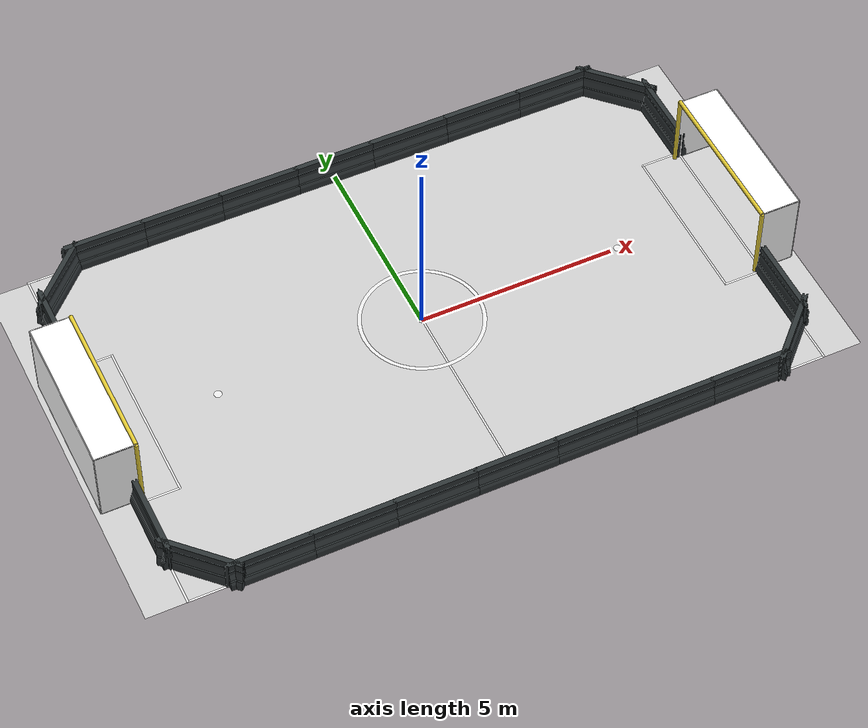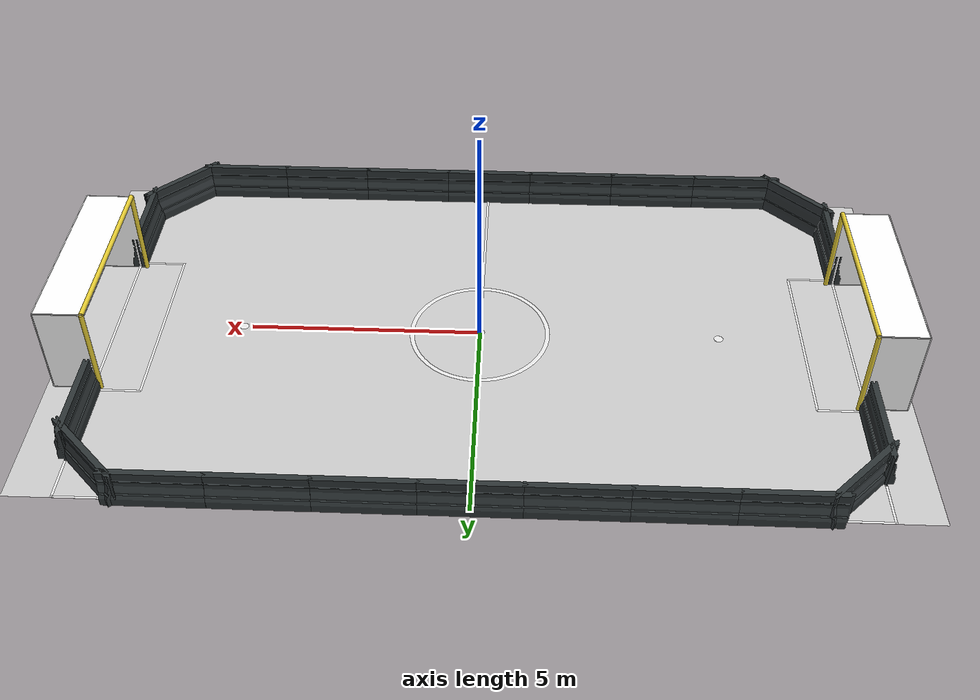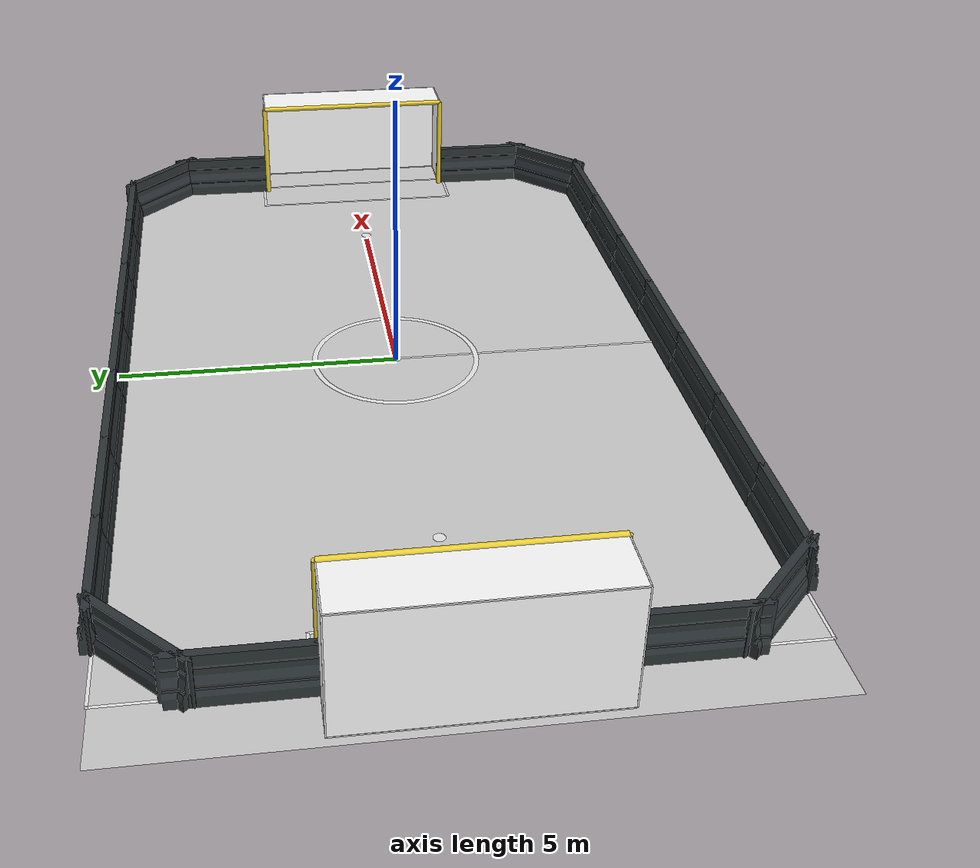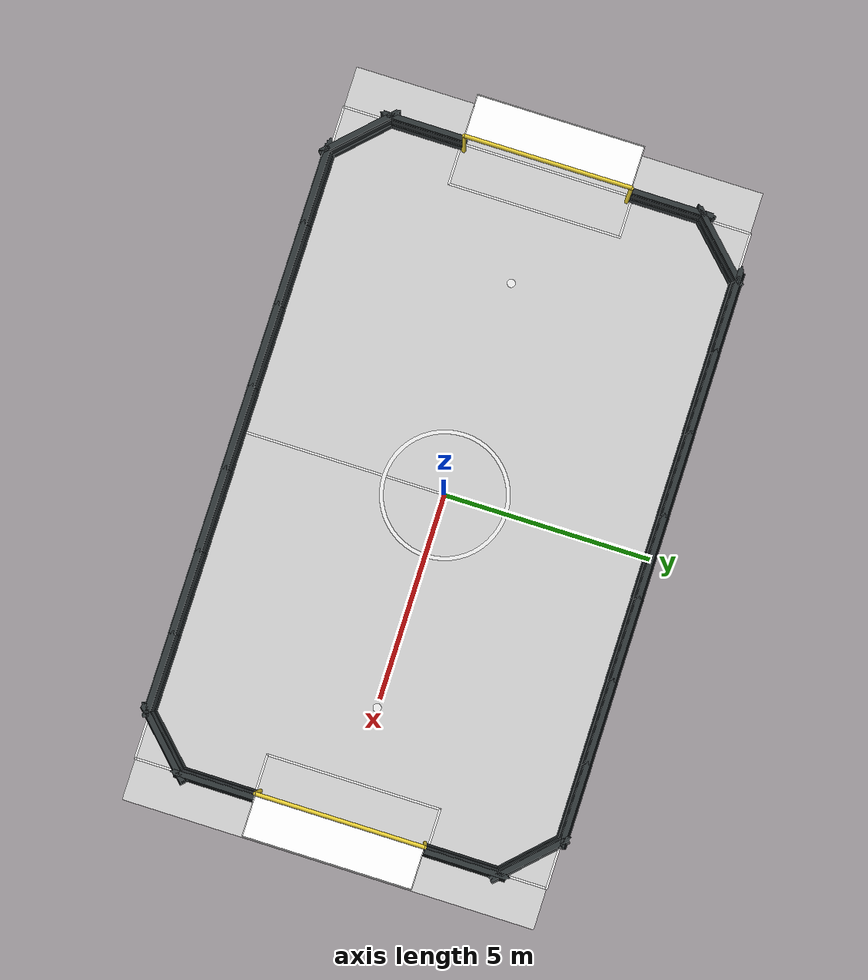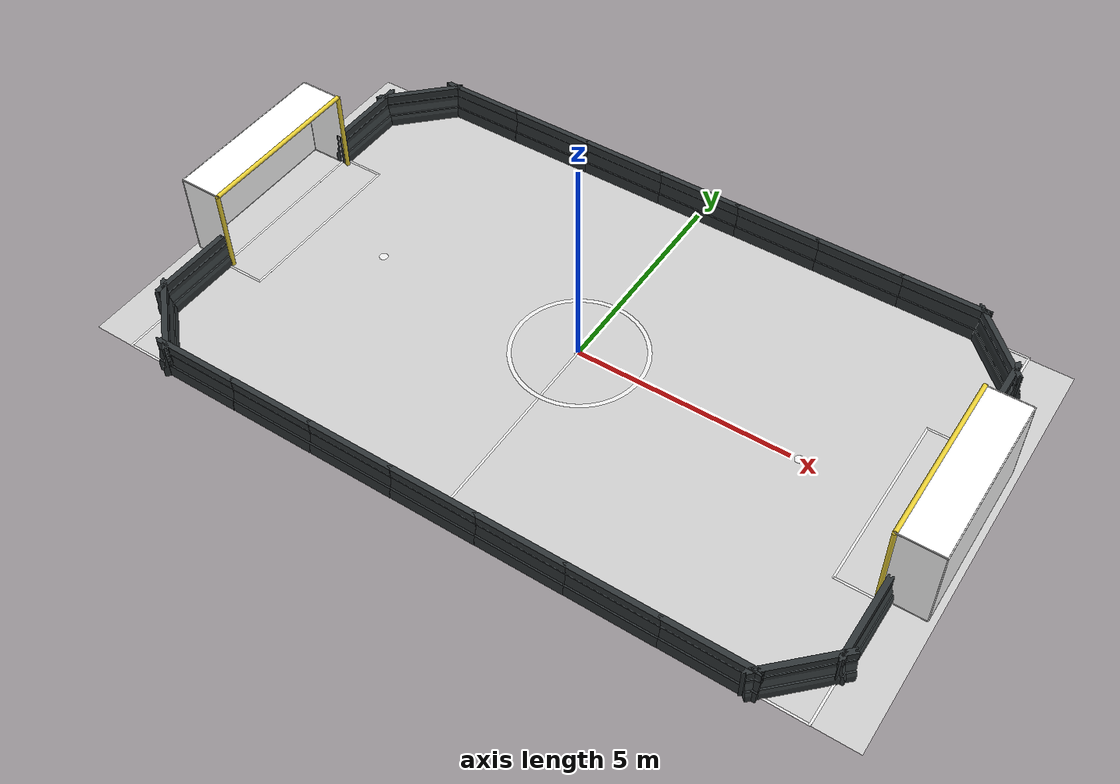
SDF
<?xml version='1.0'?>
<sdf version='1.7'>
  <model name='Soccer_Field_walls'>
    <model name='Barrier'>
      <link name='link'>
        <self_collide>0</self_collide>
        <enable_wind>0</enable_wind>
        <kinematic>0</kinematic>
        <pose>0 0 0 0 -0 0</pose>
        <gravity>1</gravity>
        <inertial>
          <mass>1</mass>
          <pose>0 0 0 0 -0 0</pose>
          <inertia>
            <ixx>1</ixx>
            <ixy>0</ixy>
            <ixz>0</ixz>
            <iyy>1</iyy>
            <iyz>0</iyz>
            <izz>1</izz>
          </inertia>
        </inertial>
        <visual name='visual'>
          <geometry>
            <mesh>
              <uri>model://drc_practice_orange_jersey_barrier/meshes/jersey_barrier.dae</uri>
              <scale>0.5 1.15 0.75</scale>
            </mesh>
          </geometry>
          <material>
            <shader type='pixel'>
              <normal_map>__default__</normal_map>
            </shader>
            <script>
              <name>ModelPreview_8::link::visual_MATERIAL_</name>
              <uri>__default__</uri>
            </script>
            <ambient>0.533 0.541 0.522 1</ambient>
            <diffuse>0.18 0.204 0.212 1</diffuse>
            <specular>0 0 0 1</specular>
            <emissive>0 0 0 1</emissive>
          </material>
          <pose>0 0 0 0 -0 0</pose>
          <transparency>0</transparency>
          <cast_shadows>1</cast_shadows>
        </visual>
        <collision name='collision'>
          <laser_retro>0</laser_retro>
          <max_contacts>10</max_contacts>
          <pose>0 0 0 0 -0 0</pose>
          <geometry>
            <mesh>
              <uri>/home/llyttle/.gazebo/models/drc_practice_orange_jersey_barrier/meshes/jersey_barrier.dae</uri>
              <scale>0.5 1.15 0.75</scale>
            </mesh>
          </geometry>
          <surface>
            <friction>
              <ode>
                <mu>1</mu>
                <mu2>1</mu2>
                <fdir1>0 0 0</fdir1>
                <slip1>0</slip1>
                <slip2>0</slip2>
              </ode>
              <torsional>
                <coefficient>1</coefficient>
                <patch_radius>0</patch_radius>
                <surface_radius>0</surface_radius>
                <use_patch_radius>1</use_patch_radius>
                <ode>
                  <slip>0</slip>
                </ode>
              </torsional>
            </friction>
            <bounce>
              <restitution_coefficient>0</restitution_coefficient>
              <threshold>1e+06</threshold>
            </bounce>
            <contact>
              <collide_without_contact>0</collide_without_contact>
              <collide_without_contact_bitmask>1</collide_without_contact_bitmask>
              <collide_bitmask>1</collide_bitmask>
              <ode>
                <soft_cfm>0</soft_cfm>
                <soft_erp>0.2</soft_erp>
                <kp>1e+13</kp>
                <kd>1</kd>
                <max_vel>0.01</max_vel>
                <min_depth>0</min_depth>
              </ode>
              <bullet>
                <split_impulse>1</split_impulse>
                <split_impulse_penetration_threshold>-0.01</split_impulse_penetration_threshold>
                <soft_cfm>0</soft_cfm>
                <soft_erp>0.2</soft_erp>
                <kp>1e+13</kp>
                <kd>1</kd>
              </bullet>
            </contact>
          </surface>
        </collision>
      </link>
      <static>1</static>
      <allow_auto_disable>1</allow_auto_disable>
      <pose>7.99542 -2.99605 0 0 -0 0</pose>
    </model>
    <model name='Barrier_clone'>
      <link name='link'>
        <self_collide>0</self_collide>
        <enable_wind>0</enable_wind>
        <kinematic>0</kinematic>
        <pose>0 0 0 0 -0 0</pose>
        <gravity>1</gravity>
        <inertial>
          <mass>1</mass>
          <pose>0 0 0 0 -0 0</pose>
          <inertia>
            <ixx>1</ixx>
            <ixy>0</ixy>
            <ixz>0</ixz>
            <iyy>1</iyy>
            <iyz>0</iyz>
            <izz>1</izz>
          </inertia>
        </inertial>
        <visual name='visual'>
          <geometry>
            <mesh>
              <uri>model://drc_practice_orange_jersey_barrier/meshes/jersey_barrier.dae</uri>
              <scale>0.5 1.15 0.75</scale>
            </mesh>
          </geometry>
          <material>
            <shader type='pixel'>
              <normal_map>__default__</normal_map>
            </shader>
            <script>
              <name>ModelPreview_8::link::visual_MATERIAL_</name>
              <uri>__default__</uri>
            </script>
            <ambient>0.533 0.541 0.522 1</ambient>
            <diffuse>0.18 0.204 0.212 1</diffuse>
            <specular>0 0 0 1</specular>
            <emissive>0 0 0 1</emissive>
          </material>
          <pose>0 0 0 0 -0 0</pose>
          <transparency>0</transparency>
          <cast_shadows>1</cast_shadows>
        </visual>
        <collision name='collision'>
          <laser_retro>0</laser_retro>
          <max_contacts>10</max_contacts>
          <pose>0 0 0 0 -0 0</pose>
          <geometry>
            <mesh>
              <uri>/home/llyttle/.gazebo/models/drc_practice_orange_jersey_barrier/meshes/jersey_barrier.dae</uri>
              <scale>0.5 1.15 0.75</scale>
            </mesh>
          </geometry>
          <surface>
            <friction>
              <ode>
                <mu>1</mu>
                <mu2>1</mu2>
                <fdir1>0 0 0</fdir1>
                <slip1>0</slip1>
                <slip2>0</slip2>
              </ode>
              <torsional>
                <coefficient>1</coefficient>
                <patch_radius>0</patch_radius>
                <surface_radius>0</surface_radius>
                <use_patch_radius>1</use_patch_radius>
                <ode>
                  <slip>0</slip>
                </ode>
              </torsional>
            </friction>
            <bounce>
              <restitution_coefficient>0</restitution_coefficient>
              <threshold>1e+06</threshold>
            </bounce>
            <contact>
              <collide_without_contact>0</collide_without_contact>
              <collide_without_contact_bitmask>1</collide_without_contact_bitmask>
              <collide_bitmask>1</collide_bitmask>
              <ode>
                <soft_cfm>0</soft_cfm>
                <soft_erp>0.2</soft_erp>
                <kp>1e+13</kp>
                <kd>1</kd>
                <max_vel>0.01</max_vel>
                <min_depth>0</min_depth>
              </ode>
              <bullet>
                <split_impulse>1</split_impulse>
                <split_impulse_penetration_threshold>-0.01</split_impulse_penetration_threshold>
                <soft_cfm>0</soft_cfm>
                <soft_erp>0.2</soft_erp>
                <kp>1e+13</kp>
                <kd>1</kd>
              </bullet>
            </contact>
          </surface>
        </collision>
      </link>
      <static>1</static>
      <allow_auto_disable>1</allow_auto_disable>
      <pose>-8.00458 -2.99605 0 0 -0 0</pose>
    </model>
    <model name='Barrier_clone_clone'>
      <link name='link'>
        <self_collide>0</self_collide>
        <enable_wind>0</enable_wind>
        <kinematic>0</kinematic>
        <pose>0 0 0 0 -0 0</pose>
        <gravity>1</gravity>
        <inertial>
          <mass>1</mass>
          <pose>0 0 0 0 -0 0</pose>
          <inertia>
            <ixx>1</ixx>
            <ixy>0</ixy>
            <ixz>0</ixz>
            <iyy>1</iyy>
            <iyz>0</iyz>
            <izz>1</izz>
          </inertia>
        </inertial>
        <visual name='visual'>
          <geometry>
            <mesh>
              <uri>model://drc_practice_orange_jersey_barrier/meshes/jersey_barrier.dae</uri>
              <scale>0.5 1.15 0.75</scale>
            </mesh>
          </geometry>
          <material>
            <shader type='pixel'>
              <normal_map>__default__</normal_map>
            </shader>
            <script>
              <name>ModelPreview_8::link::visual_MATERIAL_</name>
              <uri>__default__</uri>
            </script>
            <ambient>0.533 0.541 0.522 1</ambient>
            <diffuse>0.18 0.204 0.212 1</diffuse>
            <specular>0 0 0 1</specular>
            <emissive>0 0 0 1</emissive>
          </material>
          <pose>0 0 0 0 -0 0</pose>
          <transparency>0</transparency>
          <cast_shadows>1</cast_shadows>
        </visual>
        <collision name='collision'>
          <laser_retro>0</laser_retro>
          <max_contacts>10</max_contacts>
          <pose>0 0 0 0 -0 0</pose>
          <geometry>
            <mesh>
              <uri>/home/llyttle/.gazebo/models/drc_practice_orange_jersey_barrier/meshes/jersey_barrier.dae</uri>
              <scale>0.5 1.15 0.75</scale>
            </mesh>
          </geometry>
          <surface>
            <friction>
              <ode>
                <mu>1</mu>
                <mu2>1</mu2>
                <fdir1>0 0 0</fdir1>
                <slip1>0</slip1>
                <slip2>0</slip2>
              </ode>
              <torsional>
                <coefficient>1</coefficient>
                <patch_radius>0</patch_radius>
                <surface_radius>0</surface_radius>
                <use_patch_radius>1</use_patch_radius>
                <ode>
                  <slip>0</slip>
                </ode>
              </torsional>
            </friction>
            <bounce>
              <restitution_coefficient>0</restitution_coefficient>
              <threshold>1e+06</threshold>
            </bounce>
            <contact>
              <collide_without_contact>0</collide_without_contact>
              <collide_without_contact_bitmask>1</collide_without_contact_bitmask>
              <collide_bitmask>1</collide_bitmask>
              <ode>
                <soft_cfm>0</soft_cfm>
                <soft_erp>0.2</soft_erp>
                <kp>1e+13</kp>
                <kd>1</kd>
                <max_vel>0.01</max_vel>
                <min_depth>0</min_depth>
              </ode>
              <bullet>
                <split_impulse>1</split_impulse>
                <split_impulse_penetration_threshold>-0.01</split_impulse_penetration_threshold>
                <soft_cfm>0</soft_cfm>
                <soft_erp>0.2</soft_erp>
                <kp>1e+13</kp>
                <kd>1</kd>
              </bullet>
            </contact>
          </surface>
        </collision>
      </link>
      <static>1</static>
      <allow_auto_disable>1</allow_auto_disable>
      <pose>5.99542 -4.99605 0 0 0 -1.5708</pose>
    </model>
    <model name='Barrier_clone_clone_0'>
      <link name='link'>
        <self_collide>0</self_collide>
        <enable_wind>0</enable_wind>
        <kinematic>0</kinematic>
        <pose>0 0 0 0 -0 0</pose>
        <gravity>1</gravity>
        <inertial>
          <mass>1</mass>
          <pose>0 0 0 0 -0 0</pose>
          <inertia>
            <ixx>1</ixx>
            <ixy>0</ixy>
            <ixz>0</ixz>
            <iyy>1</iyy>
            <iyz>0</iyz>
            <izz>1</izz>
          </inertia>
        </inertial>
        <visual name='visual'>
          <geometry>
            <mesh>
              <uri>model://drc_practice_orange_jersey_barrier/meshes/jersey_barrier.dae</uri>
              <scale>0.5 1.15 0.75</scale>
            </mesh>
          </geometry>
          <material>
            <shader type='pixel'>
              <normal_map>__default__</normal_map>
            </shader>
            <script>
              <name>ModelPreview_8::link::visual_MATERIAL_</name>
              <uri>__default__</uri>
            </script>
            <ambient>0.533 0.541 0.522 1</ambient>
            <diffuse>0.18 0.204 0.212 1</diffuse>
            <specular>0 0 0 1</specular>
            <emissive>0 0 0 1</emissive>
          </material>
          <pose>0 0 0 0 -0 0</pose>
          <transparency>0</transparency>
          <cast_shadows>1</cast_shadows>
        </visual>
        <collision name='collision'>
          <laser_retro>0</laser_retro>
          <max_contacts>10</max_contacts>
          <pose>0 0 0 0 -0 0</pose>
          <geometry>
            <mesh>
              <uri>/home/llyttle/.gazebo/models/drc_practice_orange_jersey_barrier/meshes/jersey_barrier.dae</uri>
              <scale>0.5 1.15 0.75</scale>
            </mesh>
          </geometry>
          <surface>
            <friction>
              <ode>
                <mu>1</mu>
                <mu2>1</mu2>
                <fdir1>0 0 0</fdir1>
                <slip1>0</slip1>
                <slip2>0</slip2>
              </ode>
              <torsional>
                <coefficient>1</coefficient>
                <patch_radius>0</patch_radius>
                <surface_radius>0</surface_radius>
                <use_patch_radius>1</use_patch_radius>
                <ode>
                  <slip>0</slip>
                </ode>
              </torsional>
            </friction>
            <bounce>
              <restitution_coefficient>0</restitution_coefficient>
              <threshold>1e+06</threshold>
            </bounce>
            <contact>
              <collide_without_contact>0</collide_without_contact>
              <collide_without_contact_bitmask>1</collide_without_contact_bitmask>
              <collide_bitmask>1</collide_bitmask>
              <ode>
                <soft_cfm>0</soft_cfm>
                <soft_erp>0.2</soft_erp>
                <kp>1e+13</kp>
                <kd>1</kd>
                <max_vel>0.01</max_vel>
                <min_depth>0</min_depth>
              </ode>
              <bullet>
                <split_impulse>1</split_impulse>
                <split_impulse_penetration_threshold>-0.01</split_impulse_penetration_threshold>
                <soft_cfm>0</soft_cfm>
                <soft_erp>0.2</soft_erp>
                <kp>1e+13</kp>
                <kd>1</kd>
              </bullet>
            </contact>
          </surface>
        </collision>
      </link>
      <static>1</static>
      <allow_auto_disable>1</allow_auto_disable>
      <pose>-8.00458 3.00395 0 0 0 -3.14159</pose>
    </model>
    <model name='Barrier_clone_clone_0_clone'>
      <link name='link'>
        <self_collide>0</self_collide>
        <enable_wind>0</enable_wind>
        <kinematic>0</kinematic>
        <pose>0 0 0 0 -0 0</pose>
        <gravity>1</gravity>
        <inertial>
          <mass>1</mass>
          <pose>0 0 0 0 -0 0</pose>
          <inertia>
            <ixx>1</ixx>
            <ixy>0</ixy>
            <ixz>0</ixz>
            <iyy>1</iyy>
            <iyz>0</iyz>
            <izz>1</izz>
          </inertia>
        </inertial>
        <visual name='visual'>
          <geometry>
            <mesh>
              <uri>model://drc_practice_orange_jersey_barrier/meshes/jersey_barrier.dae</uri>
              <scale>0.5 1.15 0.75</scale>
            </mesh>
          </geometry>
          <material>
            <shader type='pixel'>
              <normal_map>__default__</normal_map>
            </shader>
            <script>
              <name>ModelPreview_8::link::visual_MATERIAL_</name>
              <uri>__default__</uri>
            </script>
            <ambient>0.533 0.541 0.522 1</ambient>
            <diffuse>0.18 0.204 0.212 1</diffuse>
            <specular>0 0 0 1</specular>
            <emissive>0 0 0 1</emissive>
          </material>
          <pose>0 0 0 0 -0 0</pose>
          <transparency>0</transparency>
          <cast_shadows>1</cast_shadows>
        </visual>
        <collision name='collision'>
          <laser_retro>0</laser_retro>
          <max_contacts>10</max_contacts>
          <pose>0 0 0 0 -0 0</pose>
          <geometry>
            <mesh>
              <uri>/home/llyttle/.gazebo/models/drc_practice_orange_jersey_barrier/meshes/jersey_barrier.dae</uri>
              <scale>0.5 1.15 0.75</scale>
            </mesh>
          </geometry>
          <surface>
            <friction>
              <ode>
                <mu>1</mu>
                <mu2>1</mu2>
                <fdir1>0 0 0</fdir1>
                <slip1>0</slip1>
                <slip2>0</slip2>
              </ode>
              <torsional>
                <coefficient>1</coefficient>
                <patch_radius>0</patch_radius>
                <surface_radius>0</surface_radius>
                <use_patch_radius>1</use_patch_radius>
                <ode>
                  <slip>0</slip>
                </ode>
              </torsional>
            </friction>
            <bounce>
              <restitution_coefficient>0</restitution_coefficient>
              <threshold>1e+06</threshold>
            </bounce>
            <contact>
              <collide_without_contact>0</collide_without_contact>
              <collide_without_contact_bitmask>1</collide_without_contact_bitmask>
              <collide_bitmask>1</collide_bitmask>
              <ode>
                <soft_cfm>0</soft_cfm>
                <soft_erp>0.2</soft_erp>
                <kp>1e+13</kp>
                <kd>1</kd>
                <max_vel>0.01</max_vel>
                <min_depth>0</min_depth>
              </ode>
              <bullet>
                <split_impulse>1</split_impulse>
                <split_impulse_penetration_threshold>-0.01</split_impulse_penetration_threshold>
                <soft_cfm>0</soft_cfm>
                <soft_erp>0.2</soft_erp>
                <kp>1e+13</kp>
                <kd>1</kd>
              </bullet>
            </contact>
          </surface>
        </collision>
      </link>
      <static>1</static>
      <allow_auto_disable>1</allow_auto_disable>
      <pose>7.99542 3.00395 0 0 0 -3.14159</pose>
    </model>
    <model name='Barrier_clone_clone_clone'>
      <link name='link'>
        <self_collide>0</self_collide>
        <enable_wind>0</enable_wind>
        <kinematic>0</kinematic>
        <pose>0 0 0 0 -0 0</pose>
        <gravity>1</gravity>
        <inertial>
          <mass>1</mass>
          <pose>0 0 0 0 -0 0</pose>
          <inertia>
            <ixx>1</ixx>
            <ixy>0</ixy>
            <ixz>0</ixz>
            <iyy>1</iyy>
            <iyz>0</iyz>
            <izz>1</izz>
          </inertia>
        </inertial>
        <visual name='visual'>
          <geometry>
            <mesh>
              <uri>model://drc_practice_orange_jersey_barrier/meshes/jersey_barrier.dae</uri>
              <scale>0.5 1.15 0.75</scale>
            </mesh>
          </geometry>
          <material>
            <shader type='pixel'>
              <normal_map>__default__</normal_map>
            </shader>
            <script>
              <name>ModelPreview_8::link::visual_MATERIAL_</name>
              <uri>__default__</uri>
            </script>
            <ambient>0.533 0.541 0.522 1</ambient>
            <diffuse>0.18 0.204 0.212 1</diffuse>
            <specular>0 0 0 1</specular>
            <emissive>0 0 0 1</emissive>
          </material>
          <pose>0 0 0 0 -0 0</pose>
          <transparency>0</transparency>
          <cast_shadows>1</cast_shadows>
        </visual>
        <collision name='collision'>
          <laser_retro>0</laser_retro>
          <max_contacts>10</max_contacts>
          <pose>0 0 0 0 -0 0</pose>
          <geometry>
            <mesh>
              <uri>/home/llyttle/.gazebo/models/drc_practice_orange_jersey_barrier/meshes/jersey_barrier.dae</uri>
              <scale>0.5 1.15 0.75</scale>
            </mesh>
          </geometry>
          <surface>
            <friction>
              <ode>
                <mu>1</mu>
                <mu2>1</mu2>
                <fdir1>0 0 0</fdir1>
                <slip1>0</slip1>
                <slip2>0</slip2>
              </ode>
              <torsional>
                <coefficient>1</coefficient>
                <patch_radius>0</patch_radius>
                <surface_radius>0</surface_radius>
                <use_patch_radius>1</use_patch_radius>
                <ode>
                  <slip>0</slip>
                </ode>
              </torsional>
            </friction>
            <bounce>
              <restitution_coefficient>0</restitution_coefficient>
              <threshold>1e+06</threshold>
            </bounce>
            <contact>
              <collide_without_contact>0</collide_without_contact>
              <collide_without_contact_bitmask>1</collide_without_contact_bitmask>
              <collide_bitmask>1</collide_bitmask>
              <ode>
                <soft_cfm>0</soft_cfm>
                <soft_erp>0.2</soft_erp>
                <kp>1e+13</kp>
                <kd>1</kd>
                <max_vel>0.01</max_vel>
                <min_depth>0</min_depth>
              </ode>
              <bullet>
                <split_impulse>1</split_impulse>
                <split_impulse_penetration_threshold>-0.01</split_impulse_penetration_threshold>
                <soft_cfm>0</soft_cfm>
                <soft_erp>0.2</soft_erp>
                <kp>1e+13</kp>
                <kd>1</kd>
              </bullet>
            </contact>
          </surface>
        </collision>
      </link>
      <static>1</static>
      <allow_auto_disable>1</allow_auto_disable>
      <pose>3.99542 -4.99605 0 0 0 -1.5708</pose>
    </model>
    <model name='Barrier_clone_clone_clone_0'>
      <link name='link'>
        <self_collide>0</self_collide>
        <enable_wind>0</enable_wind>
        <kinematic>0</kinematic>
        <pose>0 0 0 0 -0 0</pose>
        <gravity>1</gravity>
        <inertial>
          <mass>1</mass>
          <pose>0 0 0 0 -0 0</pose>
          <inertia>
            <ixx>1</ixx>
            <ixy>0</ixy>
            <ixz>0</ixz>
            <iyy>1</iyy>
            <iyz>0</iyz>
            <izz>1</izz>
          </inertia>
        </inertial>
        <visual name='visual'>
          <geometry>
            <mesh>
              <uri>model://drc_practice_orange_jersey_barrier/meshes/jersey_barrier.dae</uri>
              <scale>0.5 1.15 0.75</scale>
            </mesh>
          </geometry>
          <material>
            <shader type='pixel'>
              <normal_map>__default__</normal_map>
            </shader>
            <script>
              <name>ModelPreview_8::link::visual_MATERIAL_</name>
              <uri>__default__</uri>
            </script>
            <ambient>0.533 0.541 0.522 1</ambient>
            <diffuse>0.18 0.204 0.212 1</diffuse>
            <specular>0 0 0 1</specular>
            <emissive>0 0 0 1</emissive>
          </material>
          <pose>0 0 0 0 -0 0</pose>
          <transparency>0</transparency>
          <cast_shadows>1</cast_shadows>
        </visual>
        <collision name='collision'>
          <laser_retro>0</laser_retro>
          <max_contacts>10</max_contacts>
          <pose>0 0 0 0 -0 0</pose>
          <geometry>
            <mesh>
              <uri>/home/llyttle/.gazebo/models/drc_practice_orange_jersey_barrier/meshes/jersey_barrier.dae</uri>
              <scale>0.5 1.15 0.75</scale>
            </mesh>
          </geometry>
          <surface>
            <friction>
              <ode>
                <mu>1</mu>
                <mu2>1</mu2>
                <fdir1>0 0 0</fdir1>
                <slip1>0</slip1>
                <slip2>0</slip2>
              </ode>
              <torsional>
                <coefficient>1</coefficient>
                <patch_radius>0</patch_radius>
                <surface_radius>0</surface_radius>
                <use_patch_radius>1</use_patch_radius>
                <ode>
                  <slip>0</slip>
                </ode>
              </torsional>
            </friction>
            <bounce>
              <restitution_coefficient>0</restitution_coefficient>
              <threshold>1e+06</threshold>
            </bounce>
            <contact>
              <collide_without_contact>0</collide_without_contact>
              <collide_without_contact_bitmask>1</collide_without_contact_bitmask>
              <collide_bitmask>1</collide_bitmask>
              <ode>
                <soft_cfm>0</soft_cfm>
                <soft_erp>0.2</soft_erp>
                <kp>1e+13</kp>
                <kd>1</kd>
                <max_vel>0.01</max_vel>
                <min_depth>0</min_depth>
              </ode>
              <bullet>
                <split_impulse>1</split_impulse>
                <split_impulse_penetration_threshold>-0.01</split_impulse_penetration_threshold>
                <soft_cfm>0</soft_cfm>
                <soft_erp>0.2</soft_erp>
                <kp>1e+13</kp>
                <kd>1</kd>
              </bullet>
            </contact>
          </surface>
        </collision>
      </link>
      <static>1</static>
      <allow_auto_disable>1</allow_auto_disable>
      <pose>1.99542 -4.99605 0 0 0 -1.5708</pose>
    </model>
    <model name='Barrier_clone_clone_clone_1'>
      <link name='link'>
        <self_collide>0</self_collide>
        <enable_wind>0</enable_wind>
        <kinematic>0</kinematic>
        <pose>0 0 0 0 -0 0</pose>
        <gravity>1</gravity>
        <inertial>
          <mass>1</mass>
          <pose>0 0 0 0 -0 0</pose>
          <inertia>
            <ixx>1</ixx>
            <ixy>0</ixy>
            <ixz>0</ixz>
            <iyy>1</iyy>
            <iyz>0</iyz>
            <izz>1</izz>
          </inertia>
        </inertial>
        <visual name='visual'>
          <geometry>
            <mesh>
              <uri>model://drc_practice_orange_jersey_barrier/meshes/jersey_barrier.dae</uri>
              <scale>0.5 1.15 0.75</scale>
            </mesh>
          </geometry>
          <material>
            <shader type='pixel'>
              <normal_map>__default__</normal_map>
            </shader>
            <script>
              <name>ModelPreview_8::link::visual_MATERIAL_</name>
              <uri>__default__</uri>
            </script>
            <ambient>0.533 0.541 0.522 1</ambient>
            <diffuse>0.18 0.204 0.212 1</diffuse>
            <specular>0 0 0 1</specular>
            <emissive>0 0 0 1</emissive>
          </material>
          <pose>0 0 0 0 -0 0</pose>
          <transparency>0</transparency>
          <cast_shadows>1</cast_shadows>
        </visual>
        <collision name='collision'>
          <laser_retro>0</laser_retro>
          <max_contacts>10</max_contacts>
          <pose>0 0 0 0 -0 0</pose>
          <geometry>
            <mesh>
              <uri>/home/llyttle/.gazebo/models/drc_practice_orange_jersey_barrier/meshes/jersey_barrier.dae</uri>
              <scale>0.5 1.15 0.75</scale>
            </mesh>
          </geometry>
          <surface>
            <friction>
              <ode>
                <mu>1</mu>
                <mu2>1</mu2>
                <fdir1>0 0 0</fdir1>
                <slip1>0</slip1>
                <slip2>0</slip2>
              </ode>
              <torsional>
                <coefficient>1</coefficient>
                <patch_radius>0</patch_radius>
                <surface_radius>0</surface_radius>
                <use_patch_radius>1</use_patch_radius>
                <ode>
                  <slip>0</slip>
                </ode>
              </torsional>
            </friction>
            <bounce>
              <restitution_coefficient>0</restitution_coefficient>
              <threshold>1e+06</threshold>
            </bounce>
            <contact>
              <collide_without_contact>0</collide_without_contact>
              <collide_without_contact_bitmask>1</collide_without_contact_bitmask>
              <collide_bitmask>1</collide_bitmask>
              <ode>
                <soft_cfm>0</soft_cfm>
                <soft_erp>0.2</soft_erp>
                <kp>1e+13</kp>
                <kd>1</kd>
                <max_vel>0.01</max_vel>
                <min_depth>0</min_depth>
              </ode>
              <bullet>
                <split_impulse>1</split_impulse>
                <split_impulse_penetration_threshold>-0.01</split_impulse_penetration_threshold>
                <soft_cfm>0</soft_cfm>
                <soft_erp>0.2</soft_erp>
                <kp>1e+13</kp>
                <kd>1</kd>
              </bullet>
            </contact>
          </surface>
        </collision>
      </link>
      <static>1</static>
      <allow_auto_disable>1</allow_auto_disable>
      <pose>-0.004578 -4.99605 0 0 0 -1.5708</pose>
    </model>
    <model name='Barrier_clone_clone_clone_10'>
      <link name='link'>
        <self_collide>0</self_collide>
        <enable_wind>0</enable_wind>
        <kinematic>0</kinematic>
        <pose>0 0 0 0 -0 0</pose>
        <gravity>1</gravity>
        <inertial>
          <mass>1</mass>
          <pose>0 0 0 0 -0 0</pose>
          <inertia>
            <ixx>1</ixx>
            <ixy>0</ixy>
            <ixz>0</ixz>
            <iyy>1</iyy>
            <iyz>0</iyz>
            <izz>1</izz>
          </inertia>
        </inertial>
        <visual name='visual'>
          <geometry>
            <mesh>
              <uri>model://drc_practice_orange_jersey_barrier/meshes/jersey_barrier.dae</uri>
              <scale>0.5 1.15 0.75</scale>
            </mesh>
          </geometry>
          <material>
            <shader type='pixel'>
              <normal_map>__default__</normal_map>
            </shader>
            <script>
              <name>ModelPreview_8::link::visual_MATERIAL_</name>
              <uri>__default__</uri>
            </script>
            <ambient>0.533 0.541 0.522 1</ambient>
            <diffuse>0.18 0.204 0.212 1</diffuse>
            <specular>0 0 0 1</specular>
            <emissive>0 0 0 1</emissive>
          </material>
          <pose>0 0 0 0 -0 0</pose>
          <transparency>0</transparency>
          <cast_shadows>1</cast_shadows>
        </visual>
        <collision name='collision'>
          <laser_retro>0</laser_retro>
          <max_contacts>10</max_contacts>
          <pose>0 0 0 0 -0 0</pose>
          <geometry>
            <mesh>
              <uri>/home/llyttle/.gazebo/models/drc_practice_orange_jersey_barrier/meshes/jersey_barrier.dae</uri>
              <scale>0.5 1.15 0.75</scale>
            </mesh>
          </geometry>
          <surface>
            <friction>
              <ode>
                <mu>1</mu>
                <mu2>1</mu2>
                <fdir1>0 0 0</fdir1>
                <slip1>0</slip1>
                <slip2>0</slip2>
              </ode>
              <torsional>
                <coefficient>1</coefficient>
                <patch_radius>0</patch_radius>
                <surface_radius>0</surface_radius>
                <use_patch_radius>1</use_patch_radius>
                <ode>
                  <slip>0</slip>
                </ode>
              </torsional>
            </friction>
            <bounce>
              <restitution_coefficient>0</restitution_coefficient>
              <threshold>1e+06</threshold>
            </bounce>
            <contact>
              <collide_without_contact>0</collide_without_contact>
              <collide_without_contact_bitmask>1</collide_without_contact_bitmask>
              <collide_bitmask>1</collide_bitmask>
              <ode>
                <soft_cfm>0</soft_cfm>
                <soft_erp>0.2</soft_erp>
                <kp>1e+13</kp>
                <kd>1</kd>
                <max_vel>0.01</max_vel>
                <min_depth>0</min_depth>
              </ode>
              <bullet>
                <split_impulse>1</split_impulse>
                <split_impulse_penetration_threshold>-0.01</split_impulse_penetration_threshold>
                <soft_cfm>0</soft_cfm>
                <soft_erp>0.2</soft_erp>
                <kp>1e+13</kp>
                <kd>1</kd>
              </bullet>
            </contact>
          </surface>
        </collision>
      </link>
      <static>1</static>
      <allow_auto_disable>1</allow_auto_disable>
      <pose>-4.00458 5.00395 0 0 0 -1.5708</pose>
    </model>
    <model name='Barrier_clone_clone_clone_11'>
      <link name='link'>
        <self_collide>0</self_collide>
        <enable_wind>0</enable_wind>
        <kinematic>0</kinematic>
        <pose>0 0 0 0 -0 0</pose>
        <gravity>1</gravity>
        <inertial>
          <mass>1</mass>
          <pose>0 0 0 0 -0 0</pose>
          <inertia>
            <ixx>1</ixx>
            <ixy>0</ixy>
            <ixz>0</ixz>
            <iyy>1</iyy>
            <iyz>0</iyz>
            <izz>1</izz>
          </inertia>
        </inertial>
        <visual name='visual'>
          <geometry>
            <mesh>
              <uri>model://drc_practice_orange_jersey_barrier/meshes/jersey_barrier.dae</uri>
              <scale>0.5 1.15 0.75</scale>
            </mesh>
          </geometry>
          <material>
            <shader type='pixel'>
              <normal_map>__default__</normal_map>
            </shader>
            <script>
              <name>ModelPreview_8::link::visual_MATERIAL_</name>
              <uri>__default__</uri>
            </script>
            <ambient>0.533 0.541 0.522 1</ambient>
            <diffuse>0.18 0.204 0.212 1</diffuse>
            <specular>0 0 0 1</specular>
            <emissive>0 0 0 1</emissive>
          </material>
          <pose>0 0 0 0 -0 0</pose>
          <transparency>0</transparency>
          <cast_shadows>1</cast_shadows>
        </visual>
        <collision name='collision'>
          <laser_retro>0</laser_retro>
          <max_contacts>10</max_contacts>
          <pose>0 0 0 0 -0 0</pose>
          <geometry>
            <mesh>
              <uri>/home/llyttle/.gazebo/models/drc_practice_orange_jersey_barrier/meshes/jersey_barrier.dae</uri>
              <scale>0.5 1.15 0.75</scale>
            </mesh>
          </geometry>
          <surface>
            <friction>
              <ode>
                <mu>1</mu>
                <mu2>1</mu2>
                <fdir1>0 0 0</fdir1>
                <slip1>0</slip1>
                <slip2>0</slip2>
              </ode>
              <torsional>
                <coefficient>1</coefficient>
                <patch_radius>0</patch_radius>
                <surface_radius>0</surface_radius>
                <use_patch_radius>1</use_patch_radius>
                <ode>
                  <slip>0</slip>
                </ode>
              </torsional>
            </friction>
            <bounce>
              <restitution_coefficient>0</restitution_coefficient>
              <threshold>1e+06</threshold>
            </bounce>
            <contact>
              <collide_without_contact>0</collide_without_contact>
              <collide_without_contact_bitmask>1</collide_without_contact_bitmask>
              <collide_bitmask>1</collide_bitmask>
              <ode>
                <soft_cfm>0</soft_cfm>
                <soft_erp>0.2</soft_erp>
                <kp>1e+13</kp>
                <kd>1</kd>
                <max_vel>0.01</max_vel>
                <min_depth>0</min_depth>
              </ode>
              <bullet>
                <split_impulse>1</split_impulse>
                <split_impulse_penetration_threshold>-0.01</split_impulse_penetration_threshold>
                <soft_cfm>0</soft_cfm>
                <soft_erp>0.2</soft_erp>
                <kp>1e+13</kp>
                <kd>1</kd>
              </bullet>
            </contact>
          </surface>
        </collision>
      </link>
      <static>1</static>
      <allow_auto_disable>1</allow_auto_disable>
      <pose>-6.00458 5.00395 0 0 0 -1.5708</pose>
    </model>
    <model name='Barrier_clone_clone_clone_12'>
      <link name='link'>
        <self_collide>0</self_collide>
        <enable_wind>0</enable_wind>
        <kinematic>0</kinematic>
        <pose>0 0 0 0 -0 0</pose>
        <gravity>1</gravity>
        <inertial>
          <mass>1</mass>
          <pose>0 0 0 0 -0 0</pose>
          <inertia>
            <ixx>1</ixx>
            <ixy>0</ixy>
            <ixz>0</ixz>
            <iyy>1</iyy>
            <iyz>0</iyz>
            <izz>1</izz>
          </inertia>
        </inertial>
        <visual name='visual'>
          <geometry>
            <mesh>
              <uri>model://drc_practice_orange_jersey_barrier/meshes/jersey_barrier.dae</uri>
              <scale>0.5 1.15 0.75</scale>
            </mesh>
          </geometry>
          <material>
            <shader type='pixel'>
              <normal_map>__default__</normal_map>
            </shader>
            <script>
              <name>ModelPreview_8::link::visual_MATERIAL_</name>
              <uri>__default__</uri>
            </script>
            <ambient>0.533 0.541 0.522 1</ambient>
            <diffuse>0.18 0.204 0.212 1</diffuse>
            <specular>0 0 0 1</specular>
            <emissive>0 0 0 1</emissive>
          </material>
          <pose>0 0 0 0 -0 0</pose>
          <transparency>0</transparency>
          <cast_shadows>1</cast_shadows>
        </visual>
        <collision name='collision'>
          <laser_retro>0</laser_retro>
          <max_contacts>10</max_contacts>
          <pose>0 0 0 0 -0 0</pose>
          <geometry>
            <mesh>
              <uri>/home/llyttle/.gazebo/models/drc_practice_orange_jersey_barrier/meshes/jersey_barrier.dae</uri>
              <scale>0.5 1.15 0.75</scale>
            </mesh>
          </geometry>
          <surface>
            <friction>
              <ode>
                <mu>1</mu>
                <mu2>1</mu2>
                <fdir1>0 0 0</fdir1>
                <slip1>0</slip1>
                <slip2>0</slip2>
              </ode>
              <torsional>
                <coefficient>1</coefficient>
                <patch_radius>0</patch_radius>
                <surface_radius>0</surface_radius>
                <use_patch_radius>1</use_patch_radius>
                <ode>
                  <slip>0</slip>
                </ode>
              </torsional>
            </friction>
            <bounce>
              <restitution_coefficient>0</restitution_coefficient>
              <threshold>1e+06</threshold>
            </bounce>
            <contact>
              <collide_without_contact>0</collide_without_contact>
              <collide_without_contact_bitmask>1</collide_without_contact_bitmask>
              <collide_bitmask>1</collide_bitmask>
              <ode>
                <soft_cfm>0</soft_cfm>
                <soft_erp>0.2</soft_erp>
                <kp>1e+13</kp>
                <kd>1</kd>
                <max_vel>0.01</max_vel>
                <min_depth>0</min_depth>
              </ode>
              <bullet>
                <split_impulse>1</split_impulse>
                <split_impulse_penetration_threshold>-0.01</split_impulse_penetration_threshold>
                <soft_cfm>0</soft_cfm>
                <soft_erp>0.2</soft_erp>
                <kp>1e+13</kp>
                <kd>1</kd>
              </bullet>
            </contact>
          </surface>
        </collision>
      </link>
      <static>1</static>
      <allow_auto_disable>1</allow_auto_disable>
      <pose>7.45572 -4.41021 0 0 0 -0.785402</pose>
    </model>
    <model name='Barrier_clone_clone_clone_13'>
      <link name='link'>
        <self_collide>0</self_collide>
        <enable_wind>0</enable_wind>
        <kinematic>0</kinematic>
        <pose>0 0 0 0 -0 0</pose>
        <gravity>1</gravity>
        <inertial>
          <mass>1</mass>
          <pose>0 0 0 0 -0 0</pose>
          <inertia>
            <ixx>1</ixx>
            <ixy>0</ixy>
            <ixz>0</ixz>
            <iyy>1</iyy>
            <iyz>0</iyz>
            <izz>1</izz>
          </inertia>
        </inertial>
        <visual name='visual'>
          <geometry>
            <mesh>
              <uri>model://drc_practice_orange_jersey_barrier/meshes/jersey_barrier.dae</uri>
              <scale>0.5 1.15 0.75</scale>
            </mesh>
          </geometry>
          <material>
            <shader type='pixel'>
              <normal_map>__default__</normal_map>
            </shader>
            <script>
              <name>ModelPreview_8::link::visual_MATERIAL_</name>
              <uri>__default__</uri>
            </script>
            <ambient>0.533 0.541 0.522 1</ambient>
            <diffuse>0.18 0.204 0.212 1</diffuse>
            <specular>0 0 0 1</specular>
            <emissive>0 0 0 1</emissive>
          </material>
          <pose>0 0 0 0 -0 0</pose>
          <transparency>0</transparency>
          <cast_shadows>1</cast_shadows>
        </visual>
        <collision name='collision'>
          <laser_retro>0</laser_retro>
          <max_contacts>10</max_contacts>
          <pose>0 0 0 0 -0 0</pose>
          <geometry>
            <mesh>
              <uri>/home/llyttle/.gazebo/models/drc_practice_orange_jersey_barrier/meshes/jersey_barrier.dae</uri>
              <scale>0.5 1.15 0.75</scale>
            </mesh>
          </geometry>
          <surface>
            <friction>
              <ode>
                <mu>1</mu>
                <mu2>1</mu2>
                <fdir1>0 0 0</fdir1>
                <slip1>0</slip1>
                <slip2>0</slip2>
              </ode>
              <torsional>
                <coefficient>1</coefficient>
                <patch_radius>0</patch_radius>
                <surface_radius>0</surface_radius>
                <use_patch_radius>1</use_patch_radius>
                <ode>
                  <slip>0</slip>
                </ode>
              </torsional>
            </friction>
            <bounce>
              <restitution_coefficient>0</restitution_coefficient>
              <threshold>1e+06</threshold>
            </bounce>
            <contact>
              <collide_without_contact>0</collide_without_contact>
              <collide_without_contact_bitmask>1</collide_without_contact_bitmask>
              <collide_bitmask>1</collide_bitmask>
              <ode>
                <soft_cfm>0</soft_cfm>
                <soft_erp>0.2</soft_erp>
                <kp>1e+13</kp>
                <kd>1</kd>
                <max_vel>0.01</max_vel>
                <min_depth>0</min_depth>
              </ode>
              <bullet>
                <split_impulse>1</split_impulse>
                <split_impulse_penetration_threshold>-0.01</split_impulse_penetration_threshold>
                <soft_cfm>0</soft_cfm>
                <soft_erp>0.2</soft_erp>
                <kp>1e+13</kp>
                <kd>1</kd>
              </bullet>
            </contact>
          </surface>
        </collision>
      </link>
      <static>1</static>
      <allow_auto_disable>1</allow_auto_disable>
      <pose>7.44769 4.38043 0 0 0 -2.3562</pose>
    </model>
    <model name='Barrier_clone_clone_clone_14'>
      <link name='link'>
        <self_collide>0</self_collide>
        <enable_wind>0</enable_wind>
        <kinematic>0</kinematic>
        <pose>0 0 0 0 -0 0</pose>
        <gravity>1</gravity>
        <inertial>
          <mass>1</mass>
          <pose>0 0 0 0 -0 0</pose>
          <inertia>
            <ixx>1</ixx>
            <ixy>0</ixy>
            <ixz>0</ixz>
            <iyy>1</iyy>
            <iyz>0</iyz>
            <izz>1</izz>
          </inertia>
        </inertial>
        <visual name='visual'>
          <geometry>
            <mesh>
              <uri>model://drc_practice_orange_jersey_barrier/meshes/jersey_barrier.dae</uri>
              <scale>0.5 1.15 0.75</scale>
            </mesh>
          </geometry>
          <material>
            <shader type='pixel'>
              <normal_map>__default__</normal_map>
            </shader>
            <script>
              <name>ModelPreview_8::link::visual_MATERIAL_</name>
              <uri>__default__</uri>
            </script>
            <ambient>0.533 0.541 0.522 1</ambient>
            <diffuse>0.18 0.204 0.212 1</diffuse>
            <specular>0 0 0 1</specular>
            <emissive>0 0 0 1</emissive>
          </material>
          <pose>0 0 0 0 -0 0</pose>
          <transparency>0</transparency>
          <cast_shadows>1</cast_shadows>
        </visual>
        <collision name='collision'>
          <laser_retro>0</laser_retro>
          <max_contacts>10</max_contacts>
          <pose>0 0 0 0 -0 0</pose>
          <geometry>
            <mesh>
              <uri>/home/llyttle/.gazebo/models/drc_practice_orange_jersey_barrier/meshes/jersey_barrier.dae</uri>
              <scale>0.5 1.15 0.75</scale>
            </mesh>
          </geometry>
          <surface>
            <friction>
              <ode>
                <mu>1</mu>
                <mu2>1</mu2>
                <fdir1>0 0 0</fdir1>
                <slip1>0</slip1>
                <slip2>0</slip2>
              </ode>
              <torsional>
                <coefficient>1</coefficient>
                <patch_radius>0</patch_radius>
                <surface_radius>0</surface_radius>
                <use_patch_radius>1</use_patch_radius>
                <ode>
                  <slip>0</slip>
                </ode>
              </torsional>
            </friction>
            <bounce>
              <restitution_coefficient>0</restitution_coefficient>
              <threshold>1e+06</threshold>
            </bounce>
            <contact>
              <collide_without_contact>0</collide_without_contact>
              <collide_without_contact_bitmask>1</collide_without_contact_bitmask>
              <collide_bitmask>1</collide_bitmask>
              <ode>
                <soft_cfm>0</soft_cfm>
                <soft_erp>0.2</soft_erp>
                <kp>1e+13</kp>
                <kd>1</kd>
                <max_vel>0.01</max_vel>
                <min_depth>0</min_depth>
              </ode>
              <bullet>
                <split_impulse>1</split_impulse>
                <split_impulse_penetration_threshold>-0.01</split_impulse_penetration_threshold>
                <soft_cfm>0</soft_cfm>
                <soft_erp>0.2</soft_erp>
                <kp>1e+13</kp>
                <kd>1</kd>
              </bullet>
            </contact>
          </surface>
        </collision>
      </link>
      <static>1</static>
      <allow_auto_disable>1</allow_auto_disable>
      <pose>-7.39817 4.37062 0 0 0 -0.785402</pose>
    </model>
    <model name='Barrier_clone_clone_clone_15'>
      <link name='link'>
        <self_collide>0</self_collide>
        <enable_wind>0</enable_wind>
        <kinematic>0</kinematic>
        <pose>0 0 0 0 -0 0</pose>
        <gravity>1</gravity>
        <inertial>
          <mass>1</mass>
          <pose>0 0 0 0 -0 0</pose>
          <inertia>
            <ixx>1</ixx>
            <ixy>0</ixy>
            <ixz>0</ixz>
            <iyy>1</iyy>
            <iyz>0</iyz>
            <izz>1</izz>
          </inertia>
        </inertial>
        <visual name='visual'>
          <geometry>
            <mesh>
              <uri>model://drc_practice_orange_jersey_barrier/meshes/jersey_barrier.dae</uri>
              <scale>0.5 1.15 0.75</scale>
            </mesh>
          </geometry>
          <material>
            <shader type='pixel'>
              <normal_map>__default__</normal_map>
            </shader>
            <script>
              <name>ModelPreview_8::link::visual_MATERIAL_</name>
              <uri>__default__</uri>
            </script>
            <ambient>0.533 0.541 0.522 1</ambient>
            <diffuse>0.18 0.204 0.212 1</diffuse>
            <specular>0 0 0 1</specular>
            <emissive>0 0 0 1</emissive>
          </material>
          <pose>0 0 0 0 -0 0</pose>
          <transparency>0</transparency>
          <cast_shadows>1</cast_shadows>
        </visual>
        <collision name='collision'>
          <laser_retro>0</laser_retro>
          <max_contacts>10</max_contacts>
          <pose>0 0 0 0 -0 0</pose>
          <geometry>
            <mesh>
              <uri>/home/llyttle/.gazebo/models/drc_practice_orange_jersey_barrier/meshes/jersey_barrier.dae</uri>
              <scale>0.5 1.15 0.75</scale>
            </mesh>
          </geometry>
          <surface>
            <friction>
              <ode>
                <mu>1</mu>
                <mu2>1</mu2>
                <fdir1>0 0 0</fdir1>
                <slip1>0</slip1>
                <slip2>0</slip2>
              </ode>
              <torsional>
                <coefficient>1</coefficient>
                <patch_radius>0</patch_radius>
                <surface_radius>0</surface_radius>
                <use_patch_radius>1</use_patch_radius>
                <ode>
                  <slip>0</slip>
                </ode>
              </torsional>
            </friction>
            <bounce>
              <restitution_coefficient>0</restitution_coefficient>
              <threshold>1e+06</threshold>
            </bounce>
            <contact>
              <collide_without_contact>0</collide_without_contact>
              <collide_without_contact_bitmask>1</collide_without_contact_bitmask>
              <collide_bitmask>1</collide_bitmask>
              <ode>
                <soft_cfm>0</soft_cfm>
                <soft_erp>0.2</soft_erp>
                <kp>1e+13</kp>
                <kd>1</kd>
                <max_vel>0.01</max_vel>
                <min_depth>0</min_depth>
              </ode>
              <bullet>
                <split_impulse>1</split_impulse>
                <split_impulse_penetration_threshold>-0.01</split_impulse_penetration_threshold>
                <soft_cfm>0</soft_cfm>
                <soft_erp>0.2</soft_erp>
                <kp>1e+13</kp>
                <kd>1</kd>
              </bullet>
            </contact>
          </surface>
        </collision>
      </link>
      <static>1</static>
      <allow_auto_disable>1</allow_auto_disable>
      <pose>-7.41593 -4.4198 0 0 0 -2.3562</pose>
    </model>
    <model name='Barrier_clone_clone_clone_2'>
      <link name='link'>
        <self_collide>0</self_collide>
        <enable_wind>0</enable_wind>
        <kinematic>0</kinematic>
        <pose>0 0 0 0 -0 0</pose>
        <gravity>1</gravity>
        <inertial>
          <mass>1</mass>
          <pose>0 0 0 0 -0 0</pose>
          <inertia>
            <ixx>1</ixx>
            <ixy>0</ixy>
            <ixz>0</ixz>
            <iyy>1</iyy>
            <iyz>0</iyz>
            <izz>1</izz>
          </inertia>
        </inertial>
        <visual name='visual'>
          <geometry>
            <mesh>
              <uri>model://drc_practice_orange_jersey_barrier/meshes/jersey_barrier.dae</uri>
              <scale>0.5 1.15 0.75</scale>
            </mesh>
          </geometry>
          <material>
            <shader type='pixel'>
              <normal_map>__default__</normal_map>
            </shader>
            <script>
              <name>ModelPreview_8::link::visual_MATERIAL_</name>
              <uri>__default__</uri>
            </script>
            <ambient>0.533 0.541 0.522 1</ambient>
            <diffuse>0.18 0.204 0.212 1</diffuse>
            <specular>0 0 0 1</specular>
            <emissive>0 0 0 1</emissive>
          </material>
          <pose>0 0 0 0 -0 0</pose>
          <transparency>0</transparency>
          <cast_shadows>1</cast_shadows>
        </visual>
        <collision name='collision'>
          <laser_retro>0</laser_retro>
          <max_contacts>10</max_contacts>
          <pose>0 0 0 0 -0 0</pose>
          <geometry>
            <mesh>
              <uri>/home/llyttle/.gazebo/models/drc_practice_orange_jersey_barrier/meshes/jersey_barrier.dae</uri>
              <scale>0.5 1.15 0.75</scale>
            </mesh>
          </geometry>
          <surface>
            <friction>
              <ode>
                <mu>1</mu>
                <mu2>1</mu2>
                <fdir1>0 0 0</fdir1>
                <slip1>0</slip1>
                <slip2>0</slip2>
              </ode>
              <torsional>
                <coefficient>1</coefficient>
                <patch_radius>0</patch_radius>
                <surface_radius>0</surface_radius>
                <use_patch_radius>1</use_patch_radius>
                <ode>
                  <slip>0</slip>
                </ode>
              </torsional>
            </friction>
            <bounce>
              <restitution_coefficient>0</restitution_coefficient>
              <threshold>1e+06</threshold>
            </bounce>
            <contact>
              <collide_without_contact>0</collide_without_contact>
              <collide_without_contact_bitmask>1</collide_without_contact_bitmask>
              <collide_bitmask>1</collide_bitmask>
              <ode>
                <soft_cfm>0</soft_cfm>
                <soft_erp>0.2</soft_erp>
                <kp>1e+13</kp>
                <kd>1</kd>
                <max_vel>0.01</max_vel>
                <min_depth>0</min_depth>
              </ode>
              <bullet>
                <split_impulse>1</split_impulse>
                <split_impulse_penetration_threshold>-0.01</split_impulse_penetration_threshold>
                <soft_cfm>0</soft_cfm>
                <soft_erp>0.2</soft_erp>
                <kp>1e+13</kp>
                <kd>1</kd>
              </bullet>
            </contact>
          </surface>
        </collision>
      </link>
      <static>1</static>
      <allow_auto_disable>1</allow_auto_disable>
      <pose>-2.00458 -4.99605 0 0 0 -1.5708</pose>
    </model>
    <model name='Barrier_clone_clone_clone_3'>
      <link name='link'>
        <self_collide>0</self_collide>
        <enable_wind>0</enable_wind>
        <kinematic>0</kinematic>
        <pose>0 0 0 0 -0 0</pose>
        <gravity>1</gravity>
        <inertial>
          <mass>1</mass>
          <pose>0 0 0 0 -0 0</pose>
          <inertia>
            <ixx>1</ixx>
            <ixy>0</ixy>
            <ixz>0</ixz>
            <iyy>1</iyy>
            <iyz>0</iyz>
            <izz>1</izz>
          </inertia>
        </inertial>
        <visual name='visual'>
          <geometry>
            <mesh>
              <uri>model://drc_practice_orange_jersey_barrier/meshes/jersey_barrier.dae</uri>
              <scale>0.5 1.15 0.75</scale>
            </mesh>
          </geometry>
          <material>
            <shader type='pixel'>
              <normal_map>__default__</normal_map>
            </shader>
            <script>
              <name>ModelPreview_8::link::visual_MATERIAL_</name>
              <uri>__default__</uri>
            </script>
            <ambient>0.533 0.541 0.522 1</ambient>
            <diffuse>0.18 0.204 0.212 1</diffuse>
            <specular>0 0 0 1</specular>
            <emissive>0 0 0 1</emissive>
          </material>
          <pose>0 0 0 0 -0 0</pose>
          <transparency>0</transparency>
          <cast_shadows>1</cast_shadows>
        </visual>
        <collision name='collision'>
          <laser_retro>0</laser_retro>
          <max_contacts>10</max_contacts>
          <pose>0 0 0 0 -0 0</pose>
          <geometry>
            <mesh>
              <uri>/home/llyttle/.gazebo/models/drc_practice_orange_jersey_barrier/meshes/jersey_barrier.dae</uri>
              <scale>0.5 1.15 0.75</scale>
            </mesh>
          </geometry>
          <surface>
            <friction>
              <ode>
                <mu>1</mu>
                <mu2>1</mu2>
                <fdir1>0 0 0</fdir1>
                <slip1>0</slip1>
                <slip2>0</slip2>
              </ode>
              <torsional>
                <coefficient>1</coefficient>
                <patch_radius>0</patch_radius>
                <surface_radius>0</surface_radius>
                <use_patch_radius>1</use_patch_radius>
                <ode>
                  <slip>0</slip>
                </ode>
              </torsional>
            </friction>
            <bounce>
              <restitution_coefficient>0</restitution_coefficient>
              <threshold>1e+06</threshold>
            </bounce>
            <contact>
              <collide_without_contact>0</collide_without_contact>
              <collide_without_contact_bitmask>1</collide_without_contact_bitmask>
              <collide_bitmask>1</collide_bitmask>
              <ode>
                <soft_cfm>0</soft_cfm>
                <soft_erp>0.2</soft_erp>
                <kp>1e+13</kp>
                <kd>1</kd>
                <max_vel>0.01</max_vel>
                <min_depth>0</min_depth>
              </ode>
              <bullet>
                <split_impulse>1</split_impulse>
                <split_impulse_penetration_threshold>-0.01</split_impulse_penetration_threshold>
                <soft_cfm>0</soft_cfm>
                <soft_erp>0.2</soft_erp>
                <kp>1e+13</kp>
                <kd>1</kd>
              </bullet>
            </contact>
          </surface>
        </collision>
      </link>
      <static>1</static>
      <allow_auto_disable>1</allow_auto_disable>
      <pose>-4.00458 -4.99605 0 0 0 -1.5708</pose>
    </model>
    <model name='Barrier_clone_clone_clone_4'>
      <link name='link'>
        <self_collide>0</self_collide>
        <enable_wind>0</enable_wind>
        <kinematic>0</kinematic>
        <pose>0 0 0 0 -0 0</pose>
        <gravity>1</gravity>
        <inertial>
          <mass>1</mass>
          <pose>0 0 0 0 -0 0</pose>
          <inertia>
            <ixx>1</ixx>
            <ixy>0</ixy>
            <ixz>0</ixz>
            <iyy>1</iyy>
            <iyz>0</iyz>
            <izz>1</izz>
          </inertia>
        </inertial>
        <visual name='visual'>
          <geometry>
            <mesh>
              <uri>model://drc_practice_orange_jersey_barrier/meshes/jersey_barrier.dae</uri>
              <scale>0.5 1.15 0.75</scale>
            </mesh>
          </geometry>
          <material>
            <shader type='pixel'>
              <normal_map>__default__</normal_map>
            </shader>
            <script>
              <name>ModelPreview_8::link::visual_MATERIAL_</name>
              <uri>__default__</uri>
            </script>
            <ambient>0.533 0.541 0.522 1</ambient>
            <diffuse>0.18 0.204 0.212 1</diffuse>
            <specular>0 0 0 1</specular>
            <emissive>0 0 0 1</emissive>
          </material>
          <pose>0 0 0 0 -0 0</pose>
          <transparency>0</transparency>
          <cast_shadows>1</cast_shadows>
        </visual>
        <collision name='collision'>
          <laser_retro>0</laser_retro>
          <max_contacts>10</max_contacts>
          <pose>0 0 0 0 -0 0</pose>
          <geometry>
            <mesh>
              <uri>/home/llyttle/.gazebo/models/drc_practice_orange_jersey_barrier/meshes/jersey_barrier.dae</uri>
              <scale>0.5 1.15 0.75</scale>
            </mesh>
          </geometry>
          <surface>
            <friction>
              <ode>
                <mu>1</mu>
                <mu2>1</mu2>
                <fdir1>0 0 0</fdir1>
                <slip1>0</slip1>
                <slip2>0</slip2>
              </ode>
              <torsional>
                <coefficient>1</coefficient>
                <patch_radius>0</patch_radius>
                <surface_radius>0</surface_radius>
                <use_patch_radius>1</use_patch_radius>
                <ode>
                  <slip>0</slip>
                </ode>
              </torsional>
            </friction>
            <bounce>
              <restitution_coefficient>0</restitution_coefficient>
              <threshold>1e+06</threshold>
            </bounce>
            <contact>
              <collide_without_contact>0</collide_without_contact>
              <collide_without_contact_bitmask>1</collide_without_contact_bitmask>
              <collide_bitmask>1</collide_bitmask>
              <ode>
                <soft_cfm>0</soft_cfm>
                <soft_erp>0.2</soft_erp>
                <kp>1e+13</kp>
                <kd>1</kd>
                <max_vel>0.01</max_vel>
                <min_depth>0</min_depth>
              </ode>
              <bullet>
                <split_impulse>1</split_impulse>
                <split_impulse_penetration_threshold>-0.01</split_impulse_penetration_threshold>
                <soft_cfm>0</soft_cfm>
                <soft_erp>0.2</soft_erp>
                <kp>1e+13</kp>
                <kd>1</kd>
              </bullet>
            </contact>
          </surface>
        </collision>
      </link>
      <static>1</static>
      <allow_auto_disable>1</allow_auto_disable>
      <pose>-6.00458 -4.99605 0 0 0 -1.5708</pose>
    </model>
    <model name='Barrier_clone_clone_clone_5'>
      <link name='link'>
        <self_collide>0</self_collide>
        <enable_wind>0</enable_wind>
        <kinematic>0</kinematic>
        <pose>0 0 0 0 -0 0</pose>
        <gravity>1</gravity>
        <inertial>
          <mass>1</mass>
          <pose>0 0 0 0 -0 0</pose>
          <inertia>
            <ixx>1</ixx>
            <ixy>0</ixy>
            <ixz>0</ixz>
            <iyy>1</iyy>
            <iyz>0</iyz>
            <izz>1</izz>
          </inertia>
        </inertial>
        <visual name='visual'>
          <geometry>
            <mesh>
              <uri>model://drc_practice_orange_jersey_barrier/meshes/jersey_barrier.dae</uri>
              <scale>0.5 1.15 0.75</scale>
            </mesh>
          </geometry>
          <material>
            <shader type='pixel'>
              <normal_map>__default__</normal_map>
            </shader>
            <script>
              <name>ModelPreview_8::link::visual_MATERIAL_</name>
              <uri>__default__</uri>
            </script>
            <ambient>0.533 0.541 0.522 1</ambient>
            <diffuse>0.18 0.204 0.212 1</diffuse>
            <specular>0 0 0 1</specular>
            <emissive>0 0 0 1</emissive>
          </material>
          <pose>0 0 0 0 -0 0</pose>
          <transparency>0</transparency>
          <cast_shadows>1</cast_shadows>
        </visual>
        <collision name='collision'>
          <laser_retro>0</laser_retro>
          <max_contacts>10</max_contacts>
          <pose>0 0 0 0 -0 0</pose>
          <geometry>
            <mesh>
              <uri>/home/llyttle/.gazebo/models/drc_practice_orange_jersey_barrier/meshes/jersey_barrier.dae</uri>
              <scale>0.5 1.15 0.75</scale>
            </mesh>
          </geometry>
          <surface>
            <friction>
              <ode>
                <mu>1</mu>
                <mu2>1</mu2>
                <fdir1>0 0 0</fdir1>
                <slip1>0</slip1>
                <slip2>0</slip2>
              </ode>
              <torsional>
                <coefficient>1</coefficient>
                <patch_radius>0</patch_radius>
                <surface_radius>0</surface_radius>
                <use_patch_radius>1</use_patch_radius>
                <ode>
                  <slip>0</slip>
                </ode>
              </torsional>
            </friction>
            <bounce>
              <restitution_coefficient>0</restitution_coefficient>
              <threshold>1e+06</threshold>
            </bounce>
            <contact>
              <collide_without_contact>0</collide_without_contact>
              <collide_without_contact_bitmask>1</collide_without_contact_bitmask>
              <collide_bitmask>1</collide_bitmask>
              <ode>
                <soft_cfm>0</soft_cfm>
                <soft_erp>0.2</soft_erp>
                <kp>1e+13</kp>
                <kd>1</kd>
                <max_vel>0.01</max_vel>
                <min_depth>0</min_depth>
              </ode>
              <bullet>
                <split_impulse>1</split_impulse>
                <split_impulse_penetration_threshold>-0.01</split_impulse_penetration_threshold>
                <soft_cfm>0</soft_cfm>
                <soft_erp>0.2</soft_erp>
                <kp>1e+13</kp>
                <kd>1</kd>
              </bullet>
            </contact>
          </surface>
        </collision>
      </link>
      <static>1</static>
      <allow_auto_disable>1</allow_auto_disable>
      <pose>5.99542 5.00395 0 0 0 -1.5708</pose>
    </model>
    <model name='Barrier_clone_clone_clone_6'>
      <link name='link'>
        <self_collide>0</self_collide>
        <enable_wind>0</enable_wind>
        <kinematic>0</kinematic>
        <pose>0 0 0 0 -0 0</pose>
        <gravity>1</gravity>
        <inertial>
          <mass>1</mass>
          <pose>0 0 0 0 -0 0</pose>
          <inertia>
            <ixx>1</ixx>
            <ixy>0</ixy>
            <ixz>0</ixz>
            <iyy>1</iyy>
            <iyz>0</iyz>
            <izz>1</izz>
          </inertia>
        </inertial>
        <visual name='visual'>
          <geometry>
            <mesh>
              <uri>model://drc_practice_orange_jersey_barrier/meshes/jersey_barrier.dae</uri>
              <scale>0.5 1.15 0.75</scale>
            </mesh>
          </geometry>
          <material>
            <shader type='pixel'>
              <normal_map>__default__</normal_map>
            </shader>
            <script>
              <name>ModelPreview_8::link::visual_MATERIAL_</name>
              <uri>__default__</uri>
            </script>
            <ambient>0.533 0.541 0.522 1</ambient>
            <diffuse>0.18 0.204 0.212 1</diffuse>
            <specular>0 0 0 1</specular>
            <emissive>0 0 0 1</emissive>
          </material>
          <pose>0 0 0 0 -0 0</pose>
          <transparency>0</transparency>
          <cast_shadows>1</cast_shadows>
        </visual>
        <collision name='collision'>
          <laser_retro>0</laser_retro>
          <max_contacts>10</max_contacts>
          <pose>0 0 0 0 -0 0</pose>
          <geometry>
            <mesh>
              <uri>/home/llyttle/.gazebo/models/drc_practice_orange_jersey_barrier/meshes/jersey_barrier.dae</uri>
              <scale>0.5 1.15 0.75</scale>
            </mesh>
          </geometry>
          <surface>
            <friction>
              <ode>
                <mu>1</mu>
                <mu2>1</mu2>
                <fdir1>0 0 0</fdir1>
                <slip1>0</slip1>
                <slip2>0</slip2>
              </ode>
              <torsional>
                <coefficient>1</coefficient>
                <patch_radius>0</patch_radius>
                <surface_radius>0</surface_radius>
                <use_patch_radius>1</use_patch_radius>
                <ode>
                  <slip>0</slip>
                </ode>
              </torsional>
            </friction>
            <bounce>
              <restitution_coefficient>0</restitution_coefficient>
              <threshold>1e+06</threshold>
            </bounce>
            <contact>
              <collide_without_contact>0</collide_without_contact>
              <collide_without_contact_bitmask>1</collide_without_contact_bitmask>
              <collide_bitmask>1</collide_bitmask>
              <ode>
                <soft_cfm>0</soft_cfm>
                <soft_erp>0.2</soft_erp>
                <kp>1e+13</kp>
                <kd>1</kd>
                <max_vel>0.01</max_vel>
                <min_depth>0</min_depth>
              </ode>
              <bullet>
                <split_impulse>1</split_impulse>
                <split_impulse_penetration_threshold>-0.01</split_impulse_penetration_threshold>
                <soft_cfm>0</soft_cfm>
                <soft_erp>0.2</soft_erp>
                <kp>1e+13</kp>
                <kd>1</kd>
              </bullet>
            </contact>
          </surface>
        </collision>
      </link>
      <static>1</static>
      <allow_auto_disable>1</allow_auto_disable>
      <pose>3.99542 5.00395 0 0 0 -1.5708</pose>
    </model>
    <model name='Barrier_clone_clone_clone_7'>
      <link name='link'>
        <self_collide>0</self_collide>
        <enable_wind>0</enable_wind>
        <kinematic>0</kinematic>
        <pose>0 0 0 0 -0 0</pose>
        <gravity>1</gravity>
        <inertial>
          <mass>1</mass>
          <pose>0 0 0 0 -0 0</pose>
          <inertia>
            <ixx>1</ixx>
            <ixy>0</ixy>
            <ixz>0</ixz>
            <iyy>1</iyy>
            <iyz>0</iyz>
            <izz>1</izz>
          </inertia>
        </inertial>
        <visual name='visual'>
          <geometry>
            <mesh>
              <uri>model://drc_practice_orange_jersey_barrier/meshes/jersey_barrier.dae</uri>
              <scale>0.5 1.15 0.75</scale>
            </mesh>
          </geometry>
          <material>
            <shader type='pixel'>
              <normal_map>__default__</normal_map>
            </shader>
            <script>
              <name>ModelPreview_8::link::visual_MATERIAL_</name>
              <uri>__default__</uri>
            </script>
            <ambient>0.533 0.541 0.522 1</ambient>
            <diffuse>0.18 0.204 0.212 1</diffuse>
            <specular>0 0 0 1</specular>
            <emissive>0 0 0 1</emissive>
          </material>
          <pose>0 0 0 0 -0 0</pose>
          <transparency>0</transparency>
          <cast_shadows>1</cast_shadows>
        </visual>
        <collision name='collision'>
          <laser_retro>0</laser_retro>
          <max_contacts>10</max_contacts>
          <pose>0 0 0 0 -0 0</pose>
          <geometry>
            <mesh>
              <uri>/home/llyttle/.gazebo/models/drc_practice_orange_jersey_barrier/meshes/jersey_barrier.dae</uri>
              <scale>0.5 1.15 0.75</scale>
            </mesh>
          </geometry>
          <surface>
            <friction>
              <ode>
                <mu>1</mu>
                <mu2>1</mu2>
                <fdir1>0 0 0</fdir1>
                <slip1>0</slip1>
                <slip2>0</slip2>
              </ode>
              <torsional>
                <coefficient>1</coefficient>
                <patch_radius>0</patch_radius>
                <surface_radius>0</surface_radius>
                <use_patch_radius>1</use_patch_radius>
                <ode>
                  <slip>0</slip>
                </ode>
              </torsional>
            </friction>
            <bounce>
              <restitution_coefficient>0</restitution_coefficient>
              <threshold>1e+06</threshold>
            </bounce>
            <contact>
              <collide_without_contact>0</collide_without_contact>
              <collide_without_contact_bitmask>1</collide_without_contact_bitmask>
              <collide_bitmask>1</collide_bitmask>
              <ode>
                <soft_cfm>0</soft_cfm>
                <soft_erp>0.2</soft_erp>
                <kp>1e+13</kp>
                <kd>1</kd>
                <max_vel>0.01</max_vel>
                <min_depth>0</min_depth>
              </ode>
              <bullet>
                <split_impulse>1</split_impulse>
                <split_impulse_penetration_threshold>-0.01</split_impulse_penetration_threshold>
                <soft_cfm>0</soft_cfm>
                <soft_erp>0.2</soft_erp>
                <kp>1e+13</kp>
                <kd>1</kd>
              </bullet>
            </contact>
          </surface>
        </collision>
      </link>
      <static>1</static>
      <allow_auto_disable>1</allow_auto_disable>
      <pose>1.99542 5.00395 0 0 0 -1.5708</pose>
    </model>
    <model name='Barrier_clone_clone_clone_8'>
      <link name='link'>
        <self_collide>0</self_collide>
        <enable_wind>0</enable_wind>
        <kinematic>0</kinematic>
        <pose>0 0 0 0 -0 0</pose>
        <gravity>1</gravity>
        <inertial>
          <mass>1</mass>
          <pose>0 0 0 0 -0 0</pose>
          <inertia>
            <ixx>1</ixx>
            <ixy>0</ixy>
            <ixz>0</ixz>
            <iyy>1</iyy>
            <iyz>0</iyz>
            <izz>1</izz>
          </inertia>
        </inertial>
        <visual name='visual'>
          <geometry>
            <mesh>
              <uri>model://drc_practice_orange_jersey_barrier/meshes/jersey_barrier.dae</uri>
              <scale>0.5 1.15 0.75</scale>
            </mesh>
          </geometry>
          <material>
            <shader type='pixel'>
              <normal_map>__default__</normal_map>
            </shader>
            <script>
              <name>ModelPreview_8::link::visual_MATERIAL_</name>
              <uri>__default__</uri>
            </script>
            <ambient>0.533 0.541 0.522 1</ambient>
            <diffuse>0.18 0.204 0.212 1</diffuse>
            <specular>0 0 0 1</specular>
            <emissive>0 0 0 1</emissive>
          </material>
          <pose>0 0 0 0 -0 0</pose>
          <transparency>0</transparency>
          <cast_shadows>1</cast_shadows>
        </visual>
        <collision name='collision'>
          <laser_retro>0</laser_retro>
          <max_contacts>10</max_contacts>
          <pose>0 0 0 0 -0 0</pose>
          <geometry>
            <mesh>
              <uri>/home/llyttle/.gazebo/models/drc_practice_orange_jersey_barrier/meshes/jersey_barrier.dae</uri>
              <scale>0.5 1.15 0.75</scale>
            </mesh>
          </geometry>
          <surface>
            <friction>
              <ode>
                <mu>1</mu>
                <mu2>1</mu2>
                <fdir1>0 0 0</fdir1>
                <slip1>0</slip1>
                <slip2>0</slip2>
              </ode>
              <torsional>
                <coefficient>1</coefficient>
                <patch_radius>0</patch_radius>
                <surface_radius>0</surface_radius>
                <use_patch_radius>1</use_patch_radius>
                <ode>
                  <slip>0</slip>
                </ode>
              </torsional>
            </friction>
            <bounce>
              <restitution_coefficient>0</restitution_coefficient>
              <threshold>1e+06</threshold>
            </bounce>
            <contact>
              <collide_without_contact>0</collide_without_contact>
              <collide_without_contact_bitmask>1</collide_without_contact_bitmask>
              <collide_bitmask>1</collide_bitmask>
              <ode>
                <soft_cfm>0</soft_cfm>
                <soft_erp>0.2</soft_erp>
                <kp>1e+13</kp>
                <kd>1</kd>
                <max_vel>0.01</max_vel>
                <min_depth>0</min_depth>
              </ode>
              <bullet>
                <split_impulse>1</split_impulse>
                <split_impulse_penetration_threshold>-0.01</split_impulse_penetration_threshold>
                <soft_cfm>0</soft_cfm>
                <soft_erp>0.2</soft_erp>
                <kp>1e+13</kp>
                <kd>1</kd>
              </bullet>
            </contact>
          </surface>
        </collision>
      </link>
      <static>1</static>
      <allow_auto_disable>1</allow_auto_disable>
      <pose>-0.004578 5.00395 0 0 0 -1.5708</pose>
    </model>
    <model name='Barrier_clone_clone_clone_9'>
      <link name='link'>
        <self_collide>0</self_collide>
        <enable_wind>0</enable_wind>
        <kinematic>0</kinematic>
        <pose>0 0 0 0 -0 0</pose>
        <gravity>1</gravity>
        <inertial>
          <mass>1</mass>
          <pose>0 0 0 0 -0 0</pose>
          <inertia>
            <ixx>1</ixx>
            <ixy>0</ixy>
            <ixz>0</ixz>
            <iyy>1</iyy>
            <iyz>0</iyz>
            <izz>1</izz>
          </inertia>
        </inertial>
        <visual name='visual'>
          <geometry>
            <mesh>
              <uri>model://drc_practice_orange_jersey_barrier/meshes/jersey_barrier.dae</uri>
              <scale>0.5 1.15 0.75</scale>
            </mesh>
          </geometry>
          <material>
            <shader type='pixel'>
              <normal_map>__default__</normal_map>
            </shader>
            <script>
              <name>ModelPreview_8::link::visual_MATERIAL_</name>
              <uri>__default__</uri>
            </script>
            <ambient>0.533 0.541 0.522 1</ambient>
            <diffuse>0.18 0.204 0.212 1</diffuse>
            <specular>0 0 0 1</specular>
            <emissive>0 0 0 1</emissive>
          </material>
          <pose>0 0 0 0 -0 0</pose>
          <transparency>0</transparency>
          <cast_shadows>1</cast_shadows>
        </visual>
        <collision name='collision'>
          <laser_retro>0</laser_retro>
          <max_contacts>10</max_contacts>
          <pose>0 0 0 0 -0 0</pose>
          <geometry>
            <mesh>
              <uri>/home/llyttle/.gazebo/models/drc_practice_orange_jersey_barrier/meshes/jersey_barrier.dae</uri>
              <scale>0.5 1.15 0.75</scale>
            </mesh>
          </geometry>
          <surface>
            <friction>
              <ode>
                <mu>1</mu>
                <mu2>1</mu2>
                <fdir1>0 0 0</fdir1>
                <slip1>0</slip1>
                <slip2>0</slip2>
              </ode>
              <torsional>
                <coefficient>1</coefficient>
                <patch_radius>0</patch_radius>
                <surface_radius>0</surface_radius>
                <use_patch_radius>1</use_patch_radius>
                <ode>
                  <slip>0</slip>
                </ode>
              </torsional>
            </friction>
            <bounce>
              <restitution_coefficient>0</restitution_coefficient>
              <threshold>1e+06</threshold>
            </bounce>
            <contact>
              <collide_without_contact>0</collide_without_contact>
              <collide_without_contact_bitmask>1</collide_without_contact_bitmask>
              <collide_bitmask>1</collide_bitmask>
              <ode>
                <soft_cfm>0</soft_cfm>
                <soft_erp>0.2</soft_erp>
                <kp>1e+13</kp>
                <kd>1</kd>
                <max_vel>0.01</max_vel>
                <min_depth>0</min_depth>
              </ode>
              <bullet>
                <split_impulse>1</split_impulse>
                <split_impulse_penetration_threshold>-0.01</split_impulse_penetration_threshold>
                <soft_cfm>0</soft_cfm>
                <soft_erp>0.2</soft_erp>
                <kp>1e+13</kp>
                <kd>1</kd>
              </bullet>
            </contact>
          </surface>
        </collision>
      </link>
      <static>1</static>
      <allow_auto_disable>1</allow_auto_disable>
      <pose>-2.00458 5.00395 0 0 0 -1.5708</pose>
    </model>
    <model name='Goal'>
      <link name='left_post'>
        <pose>-0.086533 2 1 0 -0 0</pose>
        <self_collide>0</self_collide>
        <enable_wind>0</enable_wind>
        <kinematic>0</kinematic>
        <gravity>1</gravity>
        <inertial>
          <mass>1</mass>
          <pose>0 0 0 0 -0 0</pose>
          <inertia>
            <ixx>1</ixx>
            <ixy>0</ixy>
            <ixz>0</ixz>
            <iyy>1</iyy>
            <iyz>0</iyz>
            <izz>1</izz>
          </inertia>
        </inertial>
        <visual name='visual'>
          <geometry>
            <cylinder>
              <radius>0.05</radius>
              <length>2</length>
            </cylinder>
          </geometry>
          <material>
            <script>
              <uri>file://media/materials/scripts/gazebo.material</uri>
              <name>Gazebo/ZincYellow</name>
            </script>
            <shader type='pixel'>
              <normal_map>__default__</normal_map>
            </shader>
            <ambient>0.208 0.208 0.973 1</ambient>
            <diffuse>0.208 0.208 0.973 1</diffuse>
            <specular>0.208 0.208 0.973 1</specular>
            <emissive>0 0 0 1</emissive>
          </material>
          <pose>0 0 0 0 -0 0</pose>
          <transparency>0</transparency>
          <cast_shadows>1</cast_shadows>
        </visual>
        <collision name='collision'>
          <laser_retro>0</laser_retro>
          <max_contacts>10</max_contacts>
          <pose>0 0 0 0 -0 0</pose>
          <geometry>
            <cylinder>
              <radius>0.05</radius>
              <length>2</length>
            </cylinder>
          </geometry>
          <surface>
            <friction>
              <ode>
                <mu>1</mu>
                <mu2>1</mu2>
                <fdir1>0 0 0</fdir1>
                <slip1>0</slip1>
                <slip2>0</slip2>
              </ode>
              <torsional>
                <coefficient>1</coefficient>
                <patch_radius>0</patch_radius>
                <surface_radius>0</surface_radius>
                <use_patch_radius>1</use_patch_radius>
                <ode>
                  <slip>0</slip>
                </ode>
              </torsional>
            </friction>
            <bounce>
              <restitution_coefficient>0</restitution_coefficient>
              <threshold>1e+06</threshold>
            </bounce>
            <contact>
              <collide_without_contact>0</collide_without_contact>
              <collide_without_contact_bitmask>1</collide_without_contact_bitmask>
              <collide_bitmask>1</collide_bitmask>
              <ode>
                <soft_cfm>0</soft_cfm>
                <soft_erp>0.2</soft_erp>
                <kp>1e+13</kp>
                <kd>1</kd>
                <max_vel>0.01</max_vel>
                <min_depth>0</min_depth>
              </ode>
              <bullet>
                <split_impulse>1</split_impulse>
                <split_impulse_penetration_threshold>-0.01</split_impulse_penetration_threshold>
                <soft_cfm>0</soft_cfm>
                <soft_erp>0.2</soft_erp>
                <kp>1e+13</kp>
                <kd>1</kd>
              </bullet>
            </contact>
          </surface>
        </collision>
      </link>
      <link name='center_net'>
        <pose>0.913467 0 1 0 -0 0</pose>
        <self_collide>0</self_collide>
        <enable_wind>0</enable_wind>
        <kinematic>0</kinematic>
        <gravity>1</gravity>
        <inertial>
          <mass>1</mass>
          <pose>0 0 0 0 -0 0</pose>
          <inertia>
            <ixx>1</ixx>
            <ixy>0</ixy>
            <ixz>0</ixz>
            <iyy>1</iyy>
            <iyz>0</iyz>
            <izz>1</izz>
          </inertia>
        </inertial>
        <visual name='visual'>
          <geometry>
            <box>
              <size>0.01 4 2</size>
            </box>
          </geometry>
          <material>
            <script>
              <uri>model://robocup09_spl_field/materials/scripts/</uri>
              <uri>model://robocup09_spl_field/materials/textures/</uri>
              <name>RoboCup/Net</name>
            </script>
            <shader type='pixel'>
              <normal_map>__default__</normal_map>
            </shader>
            <ambient>1 1 1 1</ambient>
            <diffuse>1 1 1 1</diffuse>
            <specular>0 0 0 1</specular>
            <emissive>0 0 0 1</emissive>
          </material>
          <pose>0 0 0 0 -0 0</pose>
          <transparency>0</transparency>
          <cast_shadows>1</cast_shadows>
        </visual>
        <collision name='collision'>
          <laser_retro>0</laser_retro>
          <max_contacts>10</max_contacts>
          <pose>0 0 0 0 -0 0</pose>
          <geometry>
            <box>
              <size>0.01 4 2</size>
            </box>
          </geometry>
          <surface>
            <friction>
              <ode>
                <mu>1</mu>
                <mu2>1</mu2>
                <fdir1>0 0 0</fdir1>
                <slip1>0</slip1>
                <slip2>0</slip2>
              </ode>
              <torsional>
                <coefficient>1</coefficient>
                <patch_radius>0</patch_radius>
                <surface_radius>0</surface_radius>
                <use_patch_radius>1</use_patch_radius>
                <ode>
                  <slip>0</slip>
                </ode>
              </torsional>
            </friction>
            <bounce>
              <restitution_coefficient>0</restitution_coefficient>
              <threshold>1e+06</threshold>
            </bounce>
            <contact>
              <collide_without_contact>0</collide_without_contact>
              <collide_without_contact_bitmask>1</collide_without_contact_bitmask>
              <collide_bitmask>1</collide_bitmask>
              <ode>
                <soft_cfm>0</soft_cfm>
                <soft_erp>0.2</soft_erp>
                <kp>1e+13</kp>
                <kd>1</kd>
                <max_vel>0.01</max_vel>
                <min_depth>0</min_depth>
              </ode>
              <bullet>
                <split_impulse>1</split_impulse>
                <split_impulse_penetration_threshold>-0.01</split_impulse_penetration_threshold>
                <soft_cfm>0</soft_cfm>
                <soft_erp>0.2</soft_erp>
                <kp>1e+13</kp>
                <kd>1</kd>
              </bullet>
            </contact>
          </surface>
        </collision>
      </link>
      <link name='center_support_horiz_upper'>
        <pose>0.913467 0 2 3.14159 1.57079 3.14159</pose>
        <self_collide>0</self_collide>
        <enable_wind>0</enable_wind>
        <kinematic>0</kinematic>
        <gravity>1</gravity>
        <inertial>
          <mass>1</mass>
          <pose>0 0 0 0 -0 0</pose>
          <inertia>
            <ixx>1</ixx>
            <ixy>0</ixy>
            <ixz>0</ixz>
            <iyy>1</iyy>
            <iyz>0</iyz>
            <izz>1</izz>
          </inertia>
        </inertial>
        <visual name='visual'>
          <geometry>
            <box>
              <size>0.02 4 0.02</size>
            </box>
          </geometry>
          <material>
            <script>
              <uri>file://media/materials/scripts/gazebo.material</uri>
              <name>Gazebo/White</name>
            </script>
            <shader type='pixel'>
              <normal_map>__default__</normal_map>
            </shader>
            <ambient>1 1 1 1</ambient>
            <diffuse>1 1 1 1</diffuse>
            <specular>0 0 0 1</specular>
            <emissive>0 0 0 1</emissive>
          </material>
          <pose>0 0 0 0 -0 0</pose>
          <transparency>0</transparency>
          <cast_shadows>1</cast_shadows>
        </visual>
        <collision name='collision'>
          <laser_retro>0</laser_retro>
          <max_contacts>10</max_contacts>
          <pose>0 0 0 0 -0 0</pose>
          <geometry>
            <box>
              <size>0.02 4 0.02</size>
            </box>
          </geometry>
          <surface>
            <friction>
              <ode>
                <mu>1</mu>
                <mu2>1</mu2>
                <fdir1>0 0 0</fdir1>
                <slip1>0</slip1>
                <slip2>0</slip2>
              </ode>
              <torsional>
                <coefficient>1</coefficient>
                <patch_radius>0</patch_radius>
                <surface_radius>0</surface_radius>
                <use_patch_radius>1</use_patch_radius>
                <ode>
                  <slip>0</slip>
                </ode>
              </torsional>
            </friction>
            <bounce>
              <restitution_coefficient>0</restitution_coefficient>
              <threshold>1e+06</threshold>
            </bounce>
            <contact>
              <collide_without_contact>0</collide_without_contact>
              <collide_without_contact_bitmask>1</collide_without_contact_bitmask>
              <collide_bitmask>1</collide_bitmask>
              <ode>
                <soft_cfm>0</soft_cfm>
                <soft_erp>0.2</soft_erp>
                <kp>1e+13</kp>
                <kd>1</kd>
                <max_vel>0.01</max_vel>
                <min_depth>0</min_depth>
              </ode>
              <bullet>
                <split_impulse>1</split_impulse>
                <split_impulse_penetration_threshold>-0.01</split_impulse_penetration_threshold>
                <soft_cfm>0</soft_cfm>
                <soft_erp>0.2</soft_erp>
                <kp>1e+13</kp>
                <kd>1</kd>
              </bullet>
            </contact>
          </surface>
        </collision>
      </link>
      <link name='center_support_horiz_upper_clone'>
        <pose>0.913467 0 0 3.14159 1.57079 3.14159</pose>
        <self_collide>0</self_collide>
        <enable_wind>0</enable_wind>
        <kinematic>0</kinematic>
        <gravity>1</gravity>
        <inertial>
          <mass>1</mass>
          <pose>0 0 0 0 -0 0</pose>
          <inertia>
            <ixx>1</ixx>
            <ixy>0</ixy>
            <ixz>0</ixz>
            <iyy>1</iyy>
            <iyz>0</iyz>
            <izz>1</izz>
          </inertia>
        </inertial>
        <visual name='visual'>
          <geometry>
            <box>
              <size>0.02 4 0.02</size>
            </box>
          </geometry>
          <material>
            <script>
              <uri>file://media/materials/scripts/gazebo.material</uri>
              <name>Gazebo/White</name>
            </script>
            <shader type='pixel'>
              <normal_map>__default__</normal_map>
            </shader>
            <ambient>1 1 1 1</ambient>
            <diffuse>1 1 1 1</diffuse>
            <specular>0 0 0 1</specular>
            <emissive>0 0 0 1</emissive>
          </material>
          <pose>0 0 0 0 -0 0</pose>
          <transparency>0</transparency>
          <cast_shadows>1</cast_shadows>
        </visual>
        <collision name='collision'>
          <laser_retro>0</laser_retro>
          <max_contacts>10</max_contacts>
          <pose>0 0 0 0 -0 0</pose>
          <geometry>
            <box>
              <size>0.02 4 0.02</size>
            </box>
          </geometry>
          <surface>
            <friction>
              <ode>
                <mu>1</mu>
                <mu2>1</mu2>
                <fdir1>0 0 0</fdir1>
                <slip1>0</slip1>
                <slip2>0</slip2>
              </ode>
              <torsional>
                <coefficient>1</coefficient>
                <patch_radius>0</patch_radius>
                <surface_radius>0</surface_radius>
                <use_patch_radius>1</use_patch_radius>
                <ode>
                  <slip>0</slip>
                </ode>
              </torsional>
            </friction>
            <bounce>
              <restitution_coefficient>0</restitution_coefficient>
              <threshold>1e+06</threshold>
            </bounce>
            <contact>
              <collide_without_contact>0</collide_without_contact>
              <collide_without_contact_bitmask>1</collide_without_contact_bitmask>
              <collide_bitmask>1</collide_bitmask>
              <ode>
                <soft_cfm>0</soft_cfm>
                <soft_erp>0.2</soft_erp>
                <kp>1e+13</kp>
                <kd>1</kd>
                <max_vel>0.01</max_vel>
                <min_depth>0</min_depth>
              </ode>
              <bullet>
                <split_impulse>1</split_impulse>
                <split_impulse_penetration_threshold>-0.01</split_impulse_penetration_threshold>
                <soft_cfm>0</soft_cfm>
                <soft_erp>0.2</soft_erp>
                <kp>1e+13</kp>
                <kd>1</kd>
              </bullet>
            </contact>
          </surface>
        </collision>
      </link>
      <link name='crossbar'>
        <pose>-0.086533 0 2 1.56998 1.57 -9e-06</pose>
        <self_collide>0</self_collide>
        <enable_wind>0</enable_wind>
        <kinematic>0</kinematic>
        <gravity>1</gravity>
        <inertial>
          <mass>1</mass>
          <pose>0 0 0 0 -0 0</pose>
          <inertia>
            <ixx>1</ixx>
            <ixy>0</ixy>
            <ixz>0</ixz>
            <iyy>1</iyy>
            <iyz>0</iyz>
            <izz>1</izz>
          </inertia>
        </inertial>
        <visual name='visual'>
          <geometry>
            <cylinder>
              <radius>0.05</radius>
              <length>4</length>
            </cylinder>
          </geometry>
          <material>
            <script>
              <uri>file://media/materials/scripts/gazebo.material</uri>
              <name>Gazebo/ZincYellow</name>
            </script>
            <shader type='pixel'>
              <normal_map>__default__</normal_map>
            </shader>
            <ambient>0.973 0.973 0.973 1</ambient>
            <diffuse>0.973 0.973 0.973 1</diffuse>
            <specular>0.973 0.973 0.973	 1</specular>
            <emissive>0 0 0 1</emissive>
          </material>
          <pose>0 0 0 0 -0 0</pose>
          <transparency>0</transparency>
          <cast_shadows>1</cast_shadows>
        </visual>
        <collision name='collision'>
          <laser_retro>0</laser_retro>
          <max_contacts>10</max_contacts>
          <pose>0 0 0 0 -0 0</pose>
          <geometry>
            <cylinder>
              <radius>0.05</radius>
              <length>4</length>
            </cylinder>
          </geometry>
          <surface>
            <friction>
              <ode>
                <mu>1</mu>
                <mu2>1</mu2>
                <fdir1>0 0 0</fdir1>
                <slip1>0</slip1>
                <slip2>0</slip2>
              </ode>
              <torsional>
                <coefficient>1</coefficient>
                <patch_radius>0</patch_radius>
                <surface_radius>0</surface_radius>
                <use_patch_radius>1</use_patch_radius>
                <ode>
                  <slip>0</slip>
                </ode>
              </torsional>
            </friction>
            <bounce>
              <restitution_coefficient>0</restitution_coefficient>
              <threshold>1e+06</threshold>
            </bounce>
            <contact>
              <collide_without_contact>0</collide_without_contact>
              <collide_without_contact_bitmask>1</collide_without_contact_bitmask>
              <collide_bitmask>1</collide_bitmask>
              <ode>
                <soft_cfm>0</soft_cfm>
                <soft_erp>0.2</soft_erp>
                <kp>1e+13</kp>
                <kd>1</kd>
                <max_vel>0.01</max_vel>
                <min_depth>0</min_depth>
              </ode>
              <bullet>
                <split_impulse>1</split_impulse>
                <split_impulse_penetration_threshold>-0.01</split_impulse_penetration_threshold>
                <soft_cfm>0</soft_cfm>
                <soft_erp>0.2</soft_erp>
                <kp>1e+13</kp>
                <kd>1</kd>
              </bullet>
            </contact>
          </surface>
        </collision>
      </link>
      <link name='left_support_horiz_lower'>
        <pose>0.4 2 0 0 -0 0</pose>
        <self_collide>0</self_collide>
        <enable_wind>0</enable_wind>
        <kinematic>0</kinematic>
        <gravity>1</gravity>
        <inertial>
          <mass>1</mass>
          <pose>0 0 0 0 -0 0</pose>
          <inertia>
            <ixx>1</ixx>
            <ixy>0</ixy>
            <ixz>0</ixz>
            <iyy>1</iyy>
            <iyz>0</iyz>
            <izz>1</izz>
          </inertia>
        </inertial>
        <visual name='visual'>
          <geometry>
            <box>
              <size>1 0.02 0.02</size>
            </box>
          </geometry>
          <material>
            <script>
              <uri>file://media/materials/scripts/gazebo.material</uri>
              <name>Gazebo/White</name>
            </script>
            <shader type='pixel'>
              <normal_map>__default__</normal_map>
            </shader>
            <ambient>1 1 1 1</ambient>
            <diffuse>1 1 1 1</diffuse>
            <specular>0 0 0 1</specular>
            <emissive>0 0 0 1</emissive>
          </material>
          <pose>0 0 0 0 -0 0</pose>
          <transparency>0</transparency>
          <cast_shadows>1</cast_shadows>
        </visual>
        <collision name='collision'>
          <laser_retro>0</laser_retro>
          <max_contacts>10</max_contacts>
          <pose>0 0 0 0 -0 0</pose>
          <geometry>
            <box>
              <size>1 0.02 0.02</size>
            </box>
          </geometry>
          <surface>
            <friction>
              <ode>
                <mu>1</mu>
                <mu2>1</mu2>
                <fdir1>0 0 0</fdir1>
                <slip1>0</slip1>
                <slip2>0</slip2>
              </ode>
              <torsional>
                <coefficient>1</coefficient>
                <patch_radius>0</patch_radius>
                <surface_radius>0</surface_radius>
                <use_patch_radius>1</use_patch_radius>
                <ode>
                  <slip>0</slip>
                </ode>
              </torsional>
            </friction>
            <bounce>
              <restitution_coefficient>0</restitution_coefficient>
              <threshold>1e+06</threshold>
            </bounce>
            <contact>
              <collide_without_contact>0</collide_without_contact>
              <collide_without_contact_bitmask>1</collide_without_contact_bitmask>
              <collide_bitmask>1</collide_bitmask>
              <ode>
                <soft_cfm>0</soft_cfm>
                <soft_erp>0.2</soft_erp>
                <kp>1e+13</kp>
                <kd>1</kd>
                <max_vel>0.01</max_vel>
                <min_depth>0</min_depth>
              </ode>
              <bullet>
                <split_impulse>1</split_impulse>
                <split_impulse_penetration_threshold>-0.01</split_impulse_penetration_threshold>
                <soft_cfm>0</soft_cfm>
                <soft_erp>0.2</soft_erp>
                <kp>1e+13</kp>
                <kd>1</kd>
              </bullet>
            </contact>
          </surface>
        </collision>
      </link>
      <link name='left_support_horiz_lower_clone'>
        <pose>0.4 2 2 0 -0 0</pose>
        <self_collide>0</self_collide>
        <enable_wind>0</enable_wind>
        <kinematic>0</kinematic>
        <gravity>1</gravity>
        <inertial>
          <mass>1</mass>
          <pose>0 0 0 0 -0 0</pose>
          <inertia>
            <ixx>1</ixx>
            <ixy>0</ixy>
            <ixz>0</ixz>
            <iyy>1</iyy>
            <iyz>0</iyz>
            <izz>1</izz>
          </inertia>
        </inertial>
        <visual name='visual'>
          <geometry>
            <box>
              <size>1 0.02 0.02</size>
            </box>
          </geometry>
          <material>
            <script>
              <uri>file://media/materials/scripts/gazebo.material</uri>
              <name>Gazebo/White</name>
            </script>
            <shader type='pixel'>
              <normal_map>__default__</normal_map>
            </shader>
            <ambient>1 1 1 1</ambient>
            <diffuse>1 1 1 1</diffuse>
            <specular>0 0 0 1</specular>
            <emissive>0 0 0 1</emissive>
          </material>
          <pose>0 0 0 0 -0 0</pose>
          <transparency>0</transparency>
          <cast_shadows>1</cast_shadows>
        </visual>
        <collision name='collision'>
          <laser_retro>0</laser_retro>
          <max_contacts>10</max_contacts>
          <pose>0 0 0 0 -0 0</pose>
          <geometry>
            <box>
              <size>1 0.02 0.02</size>
            </box>
          </geometry>
          <surface>
            <friction>
              <ode>
                <mu>1</mu>
                <mu2>1</mu2>
                <fdir1>0 0 0</fdir1>
                <slip1>0</slip1>
                <slip2>0</slip2>
              </ode>
              <torsional>
                <coefficient>1</coefficient>
                <patch_radius>0</patch_radius>
                <surface_radius>0</surface_radius>
                <use_patch_radius>1</use_patch_radius>
                <ode>
                  <slip>0</slip>
                </ode>
              </torsional>
            </friction>
            <bounce>
              <restitution_coefficient>0</restitution_coefficient>
              <threshold>1e+06</threshold>
            </bounce>
            <contact>
              <collide_without_contact>0</collide_without_contact>
              <collide_without_contact_bitmask>1</collide_without_contact_bitmask>
              <collide_bitmask>1</collide_bitmask>
              <ode>
                <soft_cfm>0</soft_cfm>
                <soft_erp>0.2</soft_erp>
                <kp>1e+13</kp>
                <kd>1</kd>
                <max_vel>0.01</max_vel>
                <min_depth>0</min_depth>
              </ode>
              <bullet>
                <split_impulse>1</split_impulse>
                <split_impulse_penetration_threshold>-0.01</split_impulse_penetration_threshold>
                <soft_cfm>0</soft_cfm>
                <soft_erp>0.2</soft_erp>
                <kp>1e+13</kp>
                <kd>1</kd>
              </bullet>
            </contact>
          </surface>
        </collision>
      </link>
      <link name='left_support_horiz_lower_clone_0'>
        <pose>0.4 -2 2 0 -0 0</pose>
        <self_collide>0</self_collide>
        <enable_wind>0</enable_wind>
        <kinematic>0</kinematic>
        <gravity>1</gravity>
        <inertial>
          <mass>1</mass>
          <pose>0 0 0 0 -0 0</pose>
          <inertia>
            <ixx>1</ixx>
            <ixy>0</ixy>
            <ixz>0</ixz>
            <iyy>1</iyy>
            <iyz>0</iyz>
            <izz>1</izz>
          </inertia>
        </inertial>
        <visual name='visual'>
          <geometry>
            <box>
              <size>1 0.02 0.02</size>
            </box>
          </geometry>
          <material>
            <script>
              <uri>file://media/materials/scripts/gazebo.material</uri>
              <name>Gazebo/White</name>
            </script>
            <shader type='pixel'>
              <normal_map>__default__</normal_map>
            </shader>
            <ambient>1 1 1 1</ambient>
            <diffuse>1 1 1 1</diffuse>
            <specular>0 0 0 1</specular>
            <emissive>0 0 0 1</emissive>
          </material>
          <pose>0 0 0 0 -0 0</pose>
          <transparency>0</transparency>
          <cast_shadows>1</cast_shadows>
        </visual>
        <collision name='collision'>
          <laser_retro>0</laser_retro>
          <max_contacts>10</max_contacts>
          <pose>0 0 0 0 -0 0</pose>
          <geometry>
            <box>
              <size>1 0.02 0.02</size>
            </box>
          </geometry>
          <surface>
            <friction>
              <ode>
                <mu>1</mu>
                <mu2>1</mu2>
                <fdir1>0 0 0</fdir1>
                <slip1>0</slip1>
                <slip2>0</slip2>
              </ode>
              <torsional>
                <coefficient>1</coefficient>
                <patch_radius>0</patch_radius>
                <surface_radius>0</surface_radius>
                <use_patch_radius>1</use_patch_radius>
                <ode>
                  <slip>0</slip>
                </ode>
              </torsional>
            </friction>
            <bounce>
              <restitution_coefficient>0</restitution_coefficient>
              <threshold>1e+06</threshold>
            </bounce>
            <contact>
              <collide_without_contact>0</collide_without_contact>
              <collide_without_contact_bitmask>1</collide_without_contact_bitmask>
              <collide_bitmask>1</collide_bitmask>
              <ode>
                <soft_cfm>0</soft_cfm>
                <soft_erp>0.2</soft_erp>
                <kp>1e+13</kp>
                <kd>1</kd>
                <max_vel>0.01</max_vel>
                <min_depth>0</min_depth>
              </ode>
              <bullet>
                <split_impulse>1</split_impulse>
                <split_impulse_penetration_threshold>-0.01</split_impulse_penetration_threshold>
                <soft_cfm>0</soft_cfm>
                <soft_erp>0.2</soft_erp>
                <kp>1e+13</kp>
                <kd>1</kd>
              </bullet>
            </contact>
          </surface>
        </collision>
      </link>
      <link name='left_support_horiz_lower_clone_1'>
        <pose>0.4 -2 0 0 -0 0</pose>
        <self_collide>0</self_collide>
        <enable_wind>0</enable_wind>
        <kinematic>0</kinematic>
        <gravity>1</gravity>
        <inertial>
          <mass>1</mass>
          <pose>0 0 0 0 -0 0</pose>
          <inertia>
            <ixx>1</ixx>
            <ixy>0</ixy>
            <ixz>0</ixz>
            <iyy>1</iyy>
            <iyz>0</iyz>
            <izz>1</izz>
          </inertia>
        </inertial>
        <visual name='visual'>
          <geometry>
            <box>
              <size>1 0.02 0.02</size>
            </box>
          </geometry>
          <material>
            <script>
              <uri>file://media/materials/scripts/gazebo.material</uri>
              <name>Gazebo/White</name>
            </script>
            <shader type='pixel'>
              <normal_map>__default__</normal_map>
            </shader>
            <ambient>1 1 1 1</ambient>
            <diffuse>1 1 1 1</diffuse>
            <specular>0 0 0 1</specular>
            <emissive>0 0 0 1</emissive>
          </material>
          <pose>0 0 0 0 -0 0</pose>
          <transparency>0</transparency>
          <cast_shadows>1</cast_shadows>
        </visual>
        <collision name='collision'>
          <laser_retro>0</laser_retro>
          <max_contacts>10</max_contacts>
          <pose>0 0 0 0 -0 0</pose>
          <geometry>
            <box>
              <size>1 0.02 0.02</size>
            </box>
          </geometry>
          <surface>
            <friction>
              <ode>
                <mu>1</mu>
                <mu2>1</mu2>
                <fdir1>0 0 0</fdir1>
                <slip1>0</slip1>
                <slip2>0</slip2>
              </ode>
              <torsional>
                <coefficient>1</coefficient>
                <patch_radius>0</patch_radius>
                <surface_radius>0</surface_radius>
                <use_patch_radius>1</use_patch_radius>
                <ode>
                  <slip>0</slip>
                </ode>
              </torsional>
            </friction>
            <bounce>
              <restitution_coefficient>0</restitution_coefficient>
              <threshold>1e+06</threshold>
            </bounce>
            <contact>
              <collide_without_contact>0</collide_without_contact>
              <collide_without_contact_bitmask>1</collide_without_contact_bitmask>
              <collide_bitmask>1</collide_bitmask>
              <ode>
                <soft_cfm>0</soft_cfm>
                <soft_erp>0.2</soft_erp>
                <kp>1e+13</kp>
                <kd>1</kd>
                <max_vel>0.01</max_vel>
                <min_depth>0</min_depth>
              </ode>
              <bullet>
                <split_impulse>1</split_impulse>
                <split_impulse_penetration_threshold>-0.01</split_impulse_penetration_threshold>
                <soft_cfm>0</soft_cfm>
                <soft_erp>0.2</soft_erp>
                <kp>1e+13</kp>
                <kd>1</kd>
              </bullet>
            </contact>
          </surface>
        </collision>
      </link>
      <link name='right_net'>
        <pose>0.4 -2 1 0 -0 0</pose>
        <self_collide>0</self_collide>
        <enable_wind>0</enable_wind>
        <kinematic>0</kinematic>
        <gravity>1</gravity>
        <inertial>
          <mass>1</mass>
          <pose>0 0 0 0 -0 0</pose>
          <inertia>
            <ixx>1</ixx>
            <ixy>0</ixy>
            <ixz>0</ixz>
            <iyy>1</iyy>
            <iyz>0</iyz>
            <izz>1</izz>
          </inertia>
        </inertial>
        <visual name='visual'>
          <geometry>
            <box>
              <size>1 0.01 2</size>
            </box>
          </geometry>
          <material>
            <script>
              <uri>model://robocup09_spl_field/materials/scripts/</uri>
              <uri>model://robocup09_spl_field/materials/textures/</uri>
              <name>RoboCup/Net</name>
            </script>
            <shader type='pixel'>
              <normal_map>__default__</normal_map>
            </shader>
            <ambient>1 1 1 1</ambient>
            <diffuse>1 1 1 1</diffuse>
            <specular>0 0 0 1</specular>
            <emissive>0 0 0 1</emissive>
          </material>
          <pose>0 0 0 0 -0 0</pose>
          <transparency>0</transparency>
          <cast_shadows>1</cast_shadows>
        </visual>
        <collision name='collision'>
          <laser_retro>0</laser_retro>
          <max_contacts>10</max_contacts>
          <pose>0 0 0 0 -0 0</pose>
          <geometry>
            <box>
              <size>1 0.01 2</size>
            </box>
          </geometry>
          <surface>
            <friction>
              <ode>
                <mu>1</mu>
                <mu2>1</mu2>
                <fdir1>0 0 0</fdir1>
                <slip1>0</slip1>
                <slip2>0</slip2>
              </ode>
              <torsional>
                <coefficient>1</coefficient>
                <patch_radius>0</patch_radius>
                <surface_radius>0</surface_radius>
                <use_patch_radius>1</use_patch_radius>
                <ode>
                  <slip>0</slip>
                </ode>
              </torsional>
            </friction>
            <bounce>
              <restitution_coefficient>0</restitution_coefficient>
              <threshold>1e+06</threshold>
            </bounce>
            <contact>
              <collide_without_contact>0</collide_without_contact>
              <collide_without_contact_bitmask>1</collide_without_contact_bitmask>
              <collide_bitmask>1</collide_bitmask>
              <ode>
                <soft_cfm>0</soft_cfm>
                <soft_erp>0.2</soft_erp>
                <kp>1e+13</kp>
                <kd>1</kd>
                <max_vel>0.01</max_vel>
                <min_depth>0</min_depth>
              </ode>
              <bullet>
                <split_impulse>1</split_impulse>
                <split_impulse_penetration_threshold>-0.01</split_impulse_penetration_threshold>
                <soft_cfm>0</soft_cfm>
                <soft_erp>0.2</soft_erp>
                <kp>1e+13</kp>
                <kd>1</kd>
              </bullet>
            </contact>
          </surface>
        </collision>
      </link>
      <link name='right_net_clone'>
        <pose>0.4 2 1 0 -0 0</pose>
        <self_collide>0</self_collide>
        <enable_wind>0</enable_wind>
        <kinematic>0</kinematic>
        <gravity>1</gravity>
        <inertial>
          <mass>1</mass>
          <pose>0 0 0 0 -0 0</pose>
          <inertia>
            <ixx>1</ixx>
            <ixy>0</ixy>
            <ixz>0</ixz>
            <iyy>1</iyy>
            <iyz>0</iyz>
            <izz>1</izz>
          </inertia>
        </inertial>
        <visual name='visual'>
          <geometry>
            <box>
              <size>1 0.01 2</size>
            </box>
          </geometry>
          <material>
            <script>
              <uri>model://robocup09_spl_field/materials/scripts/</uri>
              <uri>model://robocup09_spl_field/materials/textures/</uri>
              <name>RoboCup/Net</name>
            </script>
            <shader type='pixel'>
              <normal_map>__default__</normal_map>
            </shader>
            <ambient>1 1 1 1</ambient>
            <diffuse>1 1 1 1</diffuse>
            <specular>0 0 0 1</specular>
            <emissive>0 0 0 1</emissive>
          </material>
          <pose>0 0 0 0 -0 0</pose>
          <transparency>0</transparency>
          <cast_shadows>1</cast_shadows>
        </visual>
        <collision name='collision'>
          <laser_retro>0</laser_retro>
          <max_contacts>10</max_contacts>
          <pose>0 0 0 0 -0 0</pose>
          <geometry>
            <box>
              <size>1 0.01 2</size>
            </box>
          </geometry>
          <surface>
            <friction>
              <ode>
                <mu>1</mu>
                <mu2>1</mu2>
                <fdir1>0 0 0</fdir1>
                <slip1>0</slip1>
                <slip2>0</slip2>
              </ode>
              <torsional>
                <coefficient>1</coefficient>
                <patch_radius>0</patch_radius>
                <surface_radius>0</surface_radius>
                <use_patch_radius>1</use_patch_radius>
                <ode>
                  <slip>0</slip>
                </ode>
              </torsional>
            </friction>
            <bounce>
              <restitution_coefficient>0</restitution_coefficient>
              <threshold>1e+06</threshold>
            </bounce>
            <contact>
              <collide_without_contact>0</collide_without_contact>
              <collide_without_contact_bitmask>1</collide_without_contact_bitmask>
              <collide_bitmask>1</collide_bitmask>
              <ode>
                <soft_cfm>0</soft_cfm>
                <soft_erp>0.2</soft_erp>
                <kp>1e+13</kp>
                <kd>1</kd>
                <max_vel>0.01</max_vel>
                <min_depth>0</min_depth>
              </ode>
              <bullet>
                <split_impulse>1</split_impulse>
                <split_impulse_penetration_threshold>-0.01</split_impulse_penetration_threshold>
                <soft_cfm>0</soft_cfm>
                <soft_erp>0.2</soft_erp>
                <kp>1e+13</kp>
                <kd>1</kd>
              </bullet>
            </contact>
          </surface>
        </collision>
      </link>
      <link name='right_net_clone_0'>
        <pose>0.4 0 2 -1.5708 0 0</pose>
        <self_collide>0</self_collide>
        <enable_wind>0</enable_wind>
        <kinematic>0</kinematic>
        <gravity>1</gravity>
        <inertial>
          <mass>1</mass>
          <pose>0 0 0 0 -0 0</pose>
          <inertia>
            <ixx>1</ixx>
            <ixy>0</ixy>
            <ixz>0</ixz>
            <iyy>1</iyy>
            <iyz>0</iyz>
            <izz>1</izz>
          </inertia>
        </inertial>
        <visual name='visual'>
          <geometry>
            <box>
              <size>1 0.01 4</size>
            </box>
          </geometry>
          <material>
            <script>
              <uri>model://robocup09_spl_field/materials/scripts/</uri>
              <uri>model://robocup09_spl_field/materials/textures/</uri>
              <name>RoboCup/Net</name>
            </script>
            <shader type='pixel'>
              <normal_map>__default__</normal_map>
            </shader>
            <ambient>1 1 1 1</ambient>
            <diffuse>1 1 1 1</diffuse>
            <specular>0 0 0 1</specular>
            <emissive>0 0 0 1</emissive>
          </material>
          <pose>0 0 0 0 -0 0</pose>
          <transparency>0</transparency>
          <cast_shadows>1</cast_shadows>
        </visual>
        <collision name='collision'>
          <laser_retro>0</laser_retro>
          <max_contacts>10</max_contacts>
          <pose>0 0 0 0 -0 0</pose>
          <geometry>
            <box>
              <size>1 0.01 4</size>
            </box>
          </geometry>
          <surface>
            <friction>
              <ode>
                <mu>1</mu>
                <mu2>1</mu2>
                <fdir1>0 0 0</fdir1>
                <slip1>0</slip1>
                <slip2>0</slip2>
              </ode>
              <torsional>
                <coefficient>1</coefficient>
                <patch_radius>0</patch_radius>
                <surface_radius>0</surface_radius>
                <use_patch_radius>1</use_patch_radius>
                <ode>
                  <slip>0</slip>
                </ode>
              </torsional>
            </friction>
            <bounce>
              <restitution_coefficient>0</restitution_coefficient>
              <threshold>1e+06</threshold>
            </bounce>
            <contact>
              <collide_without_contact>0</collide_without_contact>
              <collide_without_contact_bitmask>1</collide_without_contact_bitmask>
              <collide_bitmask>1</collide_bitmask>
              <ode>
                <soft_cfm>0</soft_cfm>
                <soft_erp>0.2</soft_erp>
                <kp>1e+13</kp>
                <kd>1</kd>
                <max_vel>0.01</max_vel>
                <min_depth>0</min_depth>
              </ode>
              <bullet>
                <split_impulse>1</split_impulse>
                <split_impulse_penetration_threshold>-0.01</split_impulse_penetration_threshold>
                <soft_cfm>0</soft_cfm>
                <soft_erp>0.2</soft_erp>
                <kp>1e+13</kp>
                <kd>1</kd>
              </bullet>
            </contact>
          </surface>
        </collision>
      </link>
      <link name='right_post'>
        <pose>-0.086533 -2 1 0 -0 0</pose>
        <self_collide>0</self_collide>
        <enable_wind>0</enable_wind>
        <kinematic>0</kinematic>
        <gravity>1</gravity>
        <inertial>
          <mass>1</mass>
          <pose>0 0 0 0 -0 0</pose>
          <inertia>
            <ixx>1</ixx>
            <ixy>0</ixy>
            <ixz>0</ixz>
            <iyy>1</iyy>
            <iyz>0</iyz>
            <izz>1</izz>
          </inertia>
        </inertial>
        <visual name='visual'>
          <geometry>
            <cylinder>
              <radius>0.05</radius>
              <length>2</length>
            </cylinder>
          </geometry>
          <material>
            <script>
              <uri>file://media/materials/scripts/gazebo.material</uri>
              <name>Gazebo/ZincYellow</name>
            </script>
            <shader type='pixel'>
              <normal_map>__default__</normal_map>
            </shader>
            <ambient>0.208 0.208 0.973 1</ambient>
            <diffuse>0.208 0.208 0.973 1</diffuse>
            <specular>0.208 0.208 0.973 1</specular>
            <emissive>0 0 0 1</emissive>
          </material>
          <pose>0 0 0 0 -0 0</pose>
          <transparency>0</transparency>
          <cast_shadows>1</cast_shadows>
        </visual>
        <collision name='collision'>
          <laser_retro>0</laser_retro>
          <max_contacts>10</max_contacts>
          <pose>0 0 0 0 -0 0</pose>
          <geometry>
            <cylinder>
              <radius>0.05</radius>
              <length>2</length>
            </cylinder>
          </geometry>
          <surface>
            <friction>
              <ode>
                <mu>1</mu>
                <mu2>1</mu2>
                <fdir1>0 0 0</fdir1>
                <slip1>0</slip1>
                <slip2>0</slip2>
              </ode>
              <torsional>
                <coefficient>1</coefficient>
                <patch_radius>0</patch_radius>
                <surface_radius>0</surface_radius>
                <use_patch_radius>1</use_patch_radius>
                <ode>
                  <slip>0</slip>
                </ode>
              </torsional>
            </friction>
            <bounce>
              <restitution_coefficient>0</restitution_coefficient>
              <threshold>1e+06</threshold>
            </bounce>
            <contact>
              <collide_without_contact>0</collide_without_contact>
              <collide_without_contact_bitmask>1</collide_without_contact_bitmask>
              <collide_bitmask>1</collide_bitmask>
              <ode>
                <soft_cfm>0</soft_cfm>
                <soft_erp>0.2</soft_erp>
                <kp>1e+13</kp>
                <kd>1</kd>
                <max_vel>0.01</max_vel>
                <min_depth>0</min_depth>
              </ode>
              <bullet>
                <split_impulse>1</split_impulse>
                <split_impulse_penetration_threshold>-0.01</split_impulse_penetration_threshold>
                <soft_cfm>0</soft_cfm>
                <soft_erp>0.2</soft_erp>
                <kp>1e+13</kp>
                <kd>1</kd>
              </bullet>
            </contact>
          </surface>
        </collision>
      </link>
      <link name='right_support_vertical'>
        <pose>0.913467 -2 1 3.14159 1.57079 3.14159</pose>
        <self_collide>0</self_collide>
        <enable_wind>0</enable_wind>
        <kinematic>0</kinematic>
        <gravity>1</gravity>
        <inertial>
          <mass>1</mass>
          <pose>0 0 0 0 -0 0</pose>
          <inertia>
            <ixx>1</ixx>
            <ixy>0</ixy>
            <ixz>0</ixz>
            <iyy>1</iyy>
            <iyz>0</iyz>
            <izz>1</izz>
          </inertia>
        </inertial>
        <visual name='visual'>
          <geometry>
            <box>
              <size>2 0.02 0.02</size>
            </box>
          </geometry>
          <material>
            <script>
              <uri>file://media/materials/scripts/gazebo.material</uri>
              <name>Gazebo/White</name>
            </script>
            <shader type='pixel'>
              <normal_map>__default__</normal_map>
            </shader>
            <ambient>1 1 1 1</ambient>
            <diffuse>1 1 1 1</diffuse>
            <specular>0 0 0 1</specular>
            <emissive>0 0 0 1</emissive>
          </material>
          <pose>0 0 0 0 -0 0</pose>
          <transparency>0</transparency>
          <cast_shadows>1</cast_shadows>
        </visual>
        <collision name='collision'>
          <laser_retro>0</laser_retro>
          <max_contacts>10</max_contacts>
          <pose>0 0 0 0 -0 0</pose>
          <geometry>
            <box>
              <size>2 0.02 0.02</size>
            </box>
          </geometry>
          <surface>
            <friction>
              <ode>
                <mu>1</mu>
                <mu2>1</mu2>
                <fdir1>0 0 0</fdir1>
                <slip1>0</slip1>
                <slip2>0</slip2>
              </ode>
              <torsional>
                <coefficient>1</coefficient>
                <patch_radius>0</patch_radius>
                <surface_radius>0</surface_radius>
                <use_patch_radius>1</use_patch_radius>
                <ode>
                  <slip>0</slip>
                </ode>
              </torsional>
            </friction>
            <bounce>
              <restitution_coefficient>0</restitution_coefficient>
              <threshold>1e+06</threshold>
            </bounce>
            <contact>
              <collide_without_contact>0</collide_without_contact>
              <collide_without_contact_bitmask>1</collide_without_contact_bitmask>
              <collide_bitmask>1</collide_bitmask>
              <ode>
                <soft_cfm>0</soft_cfm>
                <soft_erp>0.2</soft_erp>
                <kp>1e+13</kp>
                <kd>1</kd>
                <max_vel>0.01</max_vel>
                <min_depth>0</min_depth>
              </ode>
              <bullet>
                <split_impulse>1</split_impulse>
                <split_impulse_penetration_threshold>-0.01</split_impulse_penetration_threshold>
                <soft_cfm>0</soft_cfm>
                <soft_erp>0.2</soft_erp>
                <kp>1e+13</kp>
                <kd>1</kd>
              </bullet>
            </contact>
          </surface>
        </collision>
      </link>
      <link name='right_support_vertical_clone'>
        <pose>0.913467 2 1 3.14159 1.57079 3.14159</pose>
        <self_collide>0</self_collide>
        <enable_wind>0</enable_wind>
        <kinematic>0</kinematic>
        <gravity>1</gravity>
        <inertial>
          <mass>1</mass>
          <pose>0 0 0 0 -0 0</pose>
          <inertia>
            <ixx>1</ixx>
            <ixy>0</ixy>
            <ixz>0</ixz>
            <iyy>1</iyy>
            <iyz>0</iyz>
            <izz>1</izz>
          </inertia>
        </inertial>
        <visual name='visual'>
          <geometry>
            <box>
              <size>2 0.02 0.02</size>
            </box>
          </geometry>
          <material>
            <script>
              <uri>file://media/materials/scripts/gazebo.material</uri>
              <name>Gazebo/White</name>
            </script>
            <shader type='pixel'>
              <normal_map>__default__</normal_map>
            </shader>
            <ambient>1 1 1 1</ambient>
            <diffuse>1 1 1 1</diffuse>
            <specular>0 0 0 1</specular>
            <emissive>0 0 0 1</emissive>
          </material>
          <pose>0 0 0 0 -0 0</pose>
          <transparency>0</transparency>
          <cast_shadows>1</cast_shadows>
        </visual>
        <collision name='collision'>
          <laser_retro>0</laser_retro>
          <max_contacts>10</max_contacts>
          <pose>0 0 0 0 -0 0</pose>
          <geometry>
            <box>
              <size>2 0.02 0.02</size>
            </box>
          </geometry>
          <surface>
            <friction>
              <ode>
                <mu>1</mu>
                <mu2>1</mu2>
                <fdir1>0 0 0</fdir1>
                <slip1>0</slip1>
                <slip2>0</slip2>
              </ode>
              <torsional>
                <coefficient>1</coefficient>
                <patch_radius>0</patch_radius>
                <surface_radius>0</surface_radius>
                <use_patch_radius>1</use_patch_radius>
                <ode>
                  <slip>0</slip>
                </ode>
              </torsional>
            </friction>
            <bounce>
              <restitution_coefficient>0</restitution_coefficient>
              <threshold>1e+06</threshold>
            </bounce>
            <contact>
              <collide_without_contact>0</collide_without_contact>
              <collide_without_contact_bitmask>1</collide_without_contact_bitmask>
              <collide_bitmask>1</collide_bitmask>
              <ode>
                <soft_cfm>0</soft_cfm>
                <soft_erp>0.2</soft_erp>
                <kp>1e+13</kp>
                <kd>1</kd>
                <max_vel>0.01</max_vel>
                <min_depth>0</min_depth>
              </ode>
              <bullet>
                <split_impulse>1</split_impulse>
                <split_impulse_penetration_threshold>-0.01</split_impulse_penetration_threshold>
                <soft_cfm>0</soft_cfm>
                <soft_erp>0.2</soft_erp>
                <kp>1e+13</kp>
                <kd>1</kd>
              </bullet>
            </contact>
          </surface>
        </collision>
      </link>
      <static>1</static>
      <allow_auto_disable>1</allow_auto_disable>
      <pose>7.93623 0.003948 0 0 -0 0</pose>
    </model>
    <model name='Goal_clone'>
      <link name='left_post'>
        <pose>-0.086533 2 1 0 -0 0</pose>
        <self_collide>0</self_collide>
        <enable_wind>0</enable_wind>
        <kinematic>0</kinematic>
        <gravity>1</gravity>
        <inertial>
          <mass>1</mass>
          <pose>0 0 0 0 -0 0</pose>
          <inertia>
            <ixx>1</ixx>
            <ixy>0</ixy>
            <ixz>0</ixz>
            <iyy>1</iyy>
            <iyz>0</iyz>
            <izz>1</izz>
          </inertia>
        </inertial>
        <visual name='visual'>
          <geometry>
            <cylinder>
              <radius>0.05</radius>
              <length>2</length>
            </cylinder>
          </geometry>
          <material>
            <script>
              <uri>file://media/materials/scripts/gazebo.material</uri>
              <name>Gazebo/ZincYellow</name>
            </script>
            <shader type='pixel'>
              <normal_map>__default__</normal_map>
            </shader>
            <ambient>0.973 0.953 0.208 1</ambient>
            <diffuse>0.973 0.953 0.208 1</diffuse>
            <specular>0.973 0.953 0.208 1</specular>
            <emissive>0 0 0 1</emissive>
          </material>
          <pose>0 0 0 0 -0 0</pose>
          <transparency>0</transparency>
          <cast_shadows>1</cast_shadows>
        </visual>
        <collision name='collision'>
          <laser_retro>0</laser_retro>
          <max_contacts>10</max_contacts>
          <pose>0 0 0 0 -0 0</pose>
          <geometry>
            <cylinder>
              <radius>0.05</radius>
              <length>2</length>
            </cylinder>
          </geometry>
          <surface>
            <friction>
              <ode>
                <mu>1</mu>
                <mu2>1</mu2>
                <fdir1>0 0 0</fdir1>
                <slip1>0</slip1>
                <slip2>0</slip2>
              </ode>
              <torsional>
                <coefficient>1</coefficient>
                <patch_radius>0</patch_radius>
                <surface_radius>0</surface_radius>
                <use_patch_radius>1</use_patch_radius>
                <ode>
                  <slip>0</slip>
                </ode>
              </torsional>
            </friction>
            <bounce>
              <restitution_coefficient>0</restitution_coefficient>
              <threshold>1e+06</threshold>
            </bounce>
            <contact>
              <collide_without_contact>0</collide_without_contact>
              <collide_without_contact_bitmask>1</collide_without_contact_bitmask>
              <collide_bitmask>1</collide_bitmask>
              <ode>
                <soft_cfm>0</soft_cfm>
                <soft_erp>0.2</soft_erp>
                <kp>1e+13</kp>
                <kd>1</kd>
                <max_vel>0.01</max_vel>
                <min_depth>0</min_depth>
              </ode>
              <bullet>
                <split_impulse>1</split_impulse>
                <split_impulse_penetration_threshold>-0.01</split_impulse_penetration_threshold>
                <soft_cfm>0</soft_cfm>
                <soft_erp>0.2</soft_erp>
                <kp>1e+13</kp>
                <kd>1</kd>
              </bullet>
            </contact>
          </surface>
        </collision>
      </link>
      <link name='center_net'>
        <pose>0.913467 0 1 0 -0 0</pose>
        <self_collide>0</self_collide>
        <enable_wind>0</enable_wind>
        <kinematic>0</kinematic>
        <gravity>1</gravity>
        <inertial>
          <mass>1</mass>
          <pose>0 0 0 0 -0 0</pose>
          <inertia>
            <ixx>1</ixx>
            <ixy>0</ixy>
            <ixz>0</ixz>
            <iyy>1</iyy>
            <iyz>0</iyz>
            <izz>1</izz>
          </inertia>
        </inertial>
        <visual name='visual'>
          <geometry>
            <box>
              <size>0.01 4 2</size>
            </box>
          </geometry>
          <material>
            <script>
              <uri>model://robocup09_spl_field/materials/scripts/</uri>
              <uri>model://robocup09_spl_field/materials/textures/</uri>
              <name>RoboCup/Net</name>
            </script>
            <shader type='pixel'>
              <normal_map>__default__</normal_map>
            </shader>
            <ambient>1 1 1 1</ambient>
            <diffuse>1 1 1 1</diffuse>
            <specular>0 0 0 1</specular>
            <emissive>0 0 0 1</emissive>
          </material>
          <pose>0 0 0 0 -0 0</pose>
          <transparency>0</transparency>
          <cast_shadows>1</cast_shadows>
        </visual>
        <collision name='collision'>
          <laser_retro>0</laser_retro>
          <max_contacts>10</max_contacts>
          <pose>0 0 0 0 -0 0</pose>
          <geometry>
            <box>
              <size>0.01 4 2</size>
            </box>
          </geometry>
          <surface>
            <friction>
              <ode>
                <mu>1</mu>
                <mu2>1</mu2>
                <fdir1>0 0 0</fdir1>
                <slip1>0</slip1>
                <slip2>0</slip2>
              </ode>
              <torsional>
                <coefficient>1</coefficient>
                <patch_radius>0</patch_radius>
                <surface_radius>0</surface_radius>
                <use_patch_radius>1</use_patch_radius>
                <ode>
                  <slip>0</slip>
                </ode>
              </torsional>
            </friction>
            <bounce>
              <restitution_coefficient>0</restitution_coefficient>
              <threshold>1e+06</threshold>
            </bounce>
            <contact>
              <collide_without_contact>0</collide_without_contact>
              <collide_without_contact_bitmask>1</collide_without_contact_bitmask>
              <collide_bitmask>1</collide_bitmask>
              <ode>
                <soft_cfm>0</soft_cfm>
                <soft_erp>0.2</soft_erp>
                <kp>1e+13</kp>
                <kd>1</kd>
                <max_vel>0.01</max_vel>
                <min_depth>0</min_depth>
              </ode>
              <bullet>
                <split_impulse>1</split_impulse>
                <split_impulse_penetration_threshold>-0.01</split_impulse_penetration_threshold>
                <soft_cfm>0</soft_cfm>
                <soft_erp>0.2</soft_erp>
                <kp>1e+13</kp>
                <kd>1</kd>
              </bullet>
            </contact>
          </surface>
        </collision>
      </link>
      <link name='center_support_horiz_upper'>
        <pose>0.913467 0 2 3.14159 1.57079 3.14159</pose>
        <self_collide>0</self_collide>
        <enable_wind>0</enable_wind>
        <kinematic>0</kinematic>
        <gravity>1</gravity>
        <inertial>
          <mass>1</mass>
          <pose>0 0 0 0 -0 0</pose>
          <inertia>
            <ixx>1</ixx>
            <ixy>0</ixy>
            <ixz>0</ixz>
            <iyy>1</iyy>
            <iyz>0</iyz>
            <izz>1</izz>
          </inertia>
        </inertial>
        <visual name='visual'>
          <geometry>
            <box>
              <size>0.02 4 0.02</size>
            </box>
          </geometry>
          <material>
            <script>
              <uri>file://media/materials/scripts/gazebo.material</uri>
              <name>Gazebo/White</name>
            </script>
            <shader type='pixel'>
              <normal_map>__default__</normal_map>
            </shader>
            <ambient>1 1 1 1</ambient>
            <diffuse>1 1 1 1</diffuse>
            <specular>0 0 0 1</specular>
            <emissive>0 0 0 1</emissive>
          </material>
          <pose>0 0 0 0 -0 0</pose>
          <transparency>0</transparency>
          <cast_shadows>1</cast_shadows>
        </visual>
        <collision name='collision'>
          <laser_retro>0</laser_retro>
          <max_contacts>10</max_contacts>
          <pose>0 0 0 0 -0 0</pose>
          <geometry>
            <box>
              <size>0.02 4 0.02</size>
            </box>
          </geometry>
          <surface>
            <friction>
              <ode>
                <mu>1</mu>
                <mu2>1</mu2>
                <fdir1>0 0 0</fdir1>
                <slip1>0</slip1>
                <slip2>0</slip2>
              </ode>
              <torsional>
                <coefficient>1</coefficient>
                <patch_radius>0</patch_radius>
                <surface_radius>0</surface_radius>
                <use_patch_radius>1</use_patch_radius>
                <ode>
                  <slip>0</slip>
                </ode>
              </torsional>
            </friction>
            <bounce>
              <restitution_coefficient>0</restitution_coefficient>
              <threshold>1e+06</threshold>
            </bounce>
            <contact>
              <collide_without_contact>0</collide_without_contact>
              <collide_without_contact_bitmask>1</collide_without_contact_bitmask>
              <collide_bitmask>1</collide_bitmask>
              <ode>
                <soft_cfm>0</soft_cfm>
                <soft_erp>0.2</soft_erp>
                <kp>1e+13</kp>
                <kd>1</kd>
                <max_vel>0.01</max_vel>
                <min_depth>0</min_depth>
              </ode>
              <bullet>
                <split_impulse>1</split_impulse>
                <split_impulse_penetration_threshold>-0.01</split_impulse_penetration_threshold>
                <soft_cfm>0</soft_cfm>
                <soft_erp>0.2</soft_erp>
                <kp>1e+13</kp>
                <kd>1</kd>
              </bullet>
            </contact>
          </surface>
        </collision>
      </link>
      <link name='center_support_horiz_upper_clone'>
        <pose>0.913467 0 0 3.14159 1.57079 3.14159</pose>
        <self_collide>0</self_collide>
        <enable_wind>0</enable_wind>
        <kinematic>0</kinematic>
        <gravity>1</gravity>
        <inertial>
          <mass>1</mass>
          <pose>0 0 0 0 -0 0</pose>
          <inertia>
            <ixx>1</ixx>
            <ixy>0</ixy>
            <ixz>0</ixz>
            <iyy>1</iyy>
            <iyz>0</iyz>
            <izz>1</izz>
          </inertia>
        </inertial>
        <visual name='visual'>
          <geometry>
            <box>
              <size>0.02 4 0.02</size>
            </box>
          </geometry>
          <material>
            <script>
              <uri>file://media/materials/scripts/gazebo.material</uri>
              <name>Gazebo/White</name>
            </script>
            <shader type='pixel'>
              <normal_map>__default__</normal_map>
            </shader>
            <ambient>1 1 1 1</ambient>
            <diffuse>1 1 1 1</diffuse>
            <specular>0 0 0 1</specular>
            <emissive>0 0 0 1</emissive>
          </material>
          <pose>0 0 0 0 -0 0</pose>
          <transparency>0</transparency>
          <cast_shadows>1</cast_shadows>
        </visual>
        <collision name='collision'>
          <laser_retro>0</laser_retro>
          <max_contacts>10</max_contacts>
          <pose>0 0 0 0 -0 0</pose>
          <geometry>
            <box>
              <size>0.02 4 0.02</size>
            </box>
          </geometry>
          <surface>
            <friction>
              <ode>
                <mu>1</mu>
                <mu2>1</mu2>
                <fdir1>0 0 0</fdir1>
                <slip1>0</slip1>
                <slip2>0</slip2>
              </ode>
              <torsional>
                <coefficient>1</coefficient>
                <patch_radius>0</patch_radius>
                <surface_radius>0</surface_radius>
                <use_patch_radius>1</use_patch_radius>
                <ode>
                  <slip>0</slip>
                </ode>
              </torsional>
            </friction>
            <bounce>
              <restitution_coefficient>0</restitution_coefficient>
              <threshold>1e+06</threshold>
            </bounce>
            <contact>
              <collide_without_contact>0</collide_without_contact>
              <collide_without_contact_bitmask>1</collide_without_contact_bitmask>
              <collide_bitmask>1</collide_bitmask>
              <ode>
                <soft_cfm>0</soft_cfm>
                <soft_erp>0.2</soft_erp>
                <kp>1e+13</kp>
                <kd>1</kd>
                <max_vel>0.01</max_vel>
                <min_depth>0</min_depth>
              </ode>
              <bullet>
                <split_impulse>1</split_impulse>
                <split_impulse_penetration_threshold>-0.01</split_impulse_penetration_threshold>
                <soft_cfm>0</soft_cfm>
                <soft_erp>0.2</soft_erp>
                <kp>1e+13</kp>
                <kd>1</kd>
              </bullet>
            </contact>
          </surface>
        </collision>
      </link>
      <link name='crossbar'>
        <pose>-0.086533 0 2 1.56998 1.57 -9e-06</pose>
        <self_collide>0</self_collide>
        <enable_wind>0</enable_wind>
        <kinematic>0</kinematic>
        <gravity>1</gravity>
        <inertial>
          <mass>1</mass>
          <pose>0 0 0 0 -0 0</pose>
          <inertia>
            <ixx>1</ixx>
            <ixy>0</ixy>
            <ixz>0</ixz>
            <iyy>1</iyy>
            <iyz>0</iyz>
            <izz>1</izz>
          </inertia>
        </inertial>
        <visual name='visual'>
          <geometry>
            <cylinder>
              <radius>0.05</radius>
              <length>4</length>
            </cylinder>
          </geometry>
          <material>
            <script>
              <uri>file://media/materials/scripts/gazebo.material</uri>
              <name>Gazebo/ZincYellow</name>
            </script>
            <shader type='pixel'>
              <normal_map>__default__</normal_map>
            </shader>
            <ambient>0.973 0.973 0.973 1</ambient>
            <diffuse>0.973 0.973 0.973 1</diffuse>
            <specular>0.973 0.973 0.973 1</specular>
            <emissive>0 0 0 1</emissive>
          </material>
          <pose>0 0 0 0 -0 0</pose>
          <transparency>0</transparency>
          <cast_shadows>1</cast_shadows>
        </visual>
        <collision name='collision'>
          <laser_retro>0</laser_retro>
          <max_contacts>10</max_contacts>
          <pose>0 0 0 0 -0 0</pose>
          <geometry>
            <cylinder>
              <radius>0.05</radius>
              <length>4</length>
            </cylinder>
          </geometry>
          <surface>
            <friction>
              <ode>
                <mu>1</mu>
                <mu2>1</mu2>
                <fdir1>0 0 0</fdir1>
                <slip1>0</slip1>
                <slip2>0</slip2>
              </ode>
              <torsional>
                <coefficient>1</coefficient>
                <patch_radius>0</patch_radius>
                <surface_radius>0</surface_radius>
                <use_patch_radius>1</use_patch_radius>
                <ode>
                  <slip>0</slip>
                </ode>
              </torsional>
            </friction>
            <bounce>
              <restitution_coefficient>0</restitution_coefficient>
              <threshold>1e+06</threshold>
            </bounce>
            <contact>
              <collide_without_contact>0</collide_without_contact>
              <collide_without_contact_bitmask>1</collide_without_contact_bitmask>
              <collide_bitmask>1</collide_bitmask>
              <ode>
                <soft_cfm>0</soft_cfm>
                <soft_erp>0.2</soft_erp>
                <kp>1e+13</kp>
                <kd>1</kd>
                <max_vel>0.01</max_vel>
                <min_depth>0</min_depth>
              </ode>
              <bullet>
                <split_impulse>1</split_impulse>
                <split_impulse_penetration_threshold>-0.01</split_impulse_penetration_threshold>
                <soft_cfm>0</soft_cfm>
                <soft_erp>0.2</soft_erp>
                <kp>1e+13</kp>
                <kd>1</kd>
              </bullet>
            </contact>
          </surface>
        </collision>
      </link>
      <link name='left_support_horiz_lower'>
        <pose>0.4 2 0 0 -0 0</pose>
        <self_collide>0</self_collide>
        <enable_wind>0</enable_wind>
        <kinematic>0</kinematic>
        <gravity>1</gravity>
        <inertial>
          <mass>1</mass>
          <pose>0 0 0 0 -0 0</pose>
          <inertia>
            <ixx>1</ixx>
            <ixy>0</ixy>
            <ixz>0</ixz>
            <iyy>1</iyy>
            <iyz>0</iyz>
            <izz>1</izz>
          </inertia>
        </inertial>
        <visual name='visual'>
          <geometry>
            <box>
              <size>1 0.02 0.02</size>
            </box>
          </geometry>
          <material>
            <script>
              <uri>file://media/materials/scripts/gazebo.material</uri>
              <name>Gazebo/White</name>
            </script>
            <shader type='pixel'>
              <normal_map>__default__</normal_map>
            </shader>
            <ambient>1 1 1 1</ambient>
            <diffuse>1 1 1 1</diffuse>
            <specular>0 0 0 1</specular>
            <emissive>0 0 0 1</emissive>
          </material>
          <pose>0 0 0 0 -0 0</pose>
          <transparency>0</transparency>
          <cast_shadows>1</cast_shadows>
        </visual>
        <collision name='collision'>
          <laser_retro>0</laser_retro>
          <max_contacts>10</max_contacts>
          <pose>0 0 0 0 -0 0</pose>
          <geometry>
            <box>
              <size>1 0.02 0.02</size>
            </box>
          </geometry>
          <surface>
            <friction>
              <ode>
                <mu>1</mu>
                <mu2>1</mu2>
                <fdir1>0 0 0</fdir1>
                <slip1>0</slip1>
                <slip2>0</slip2>
              </ode>
              <torsional>
                <coefficient>1</coefficient>
                <patch_radius>0</patch_radius>
                <surface_radius>0</surface_radius>
                <use_patch_radius>1</use_patch_radius>
                <ode>
                  <slip>0</slip>
                </ode>
              </torsional>
            </friction>
            <bounce>
              <restitution_coefficient>0</restitution_coefficient>
              <threshold>1e+06</threshold>
            </bounce>
            <contact>
              <collide_without_contact>0</collide_without_contact>
              <collide_without_contact_bitmask>1</collide_without_contact_bitmask>
              <collide_bitmask>1</collide_bitmask>
              <ode>
                <soft_cfm>0</soft_cfm>
                <soft_erp>0.2</soft_erp>
                <kp>1e+13</kp>
                <kd>1</kd>
                <max_vel>0.01</max_vel>
                <min_depth>0</min_depth>
              </ode>
              <bullet>
                <split_impulse>1</split_impulse>
                <split_impulse_penetration_threshold>-0.01</split_impulse_penetration_threshold>
                <soft_cfm>0</soft_cfm>
                <soft_erp>0.2</soft_erp>
                <kp>1e+13</kp>
                <kd>1</kd>
              </bullet>
            </contact>
          </surface>
        </collision>
      </link>
      <link name='left_support_horiz_lower_clone'>
        <pose>0.4 2 2 0 -0 0</pose>
        <self_collide>0</self_collide>
        <enable_wind>0</enable_wind>
        <kinematic>0</kinematic>
        <gravity>1</gravity>
        <inertial>
          <mass>1</mass>
          <pose>0 0 0 0 -0 0</pose>
          <inertia>
            <ixx>1</ixx>
            <ixy>0</ixy>
            <ixz>0</ixz>
            <iyy>1</iyy>
            <iyz>0</iyz>
            <izz>1</izz>
          </inertia>
        </inertial>
        <visual name='visual'>
          <geometry>
            <box>
              <size>1 0.02 0.02</size>
            </box>
          </geometry>
          <material>
            <script>
              <uri>file://media/materials/scripts/gazebo.material</uri>
              <name>Gazebo/White</name>
            </script>
            <shader type='pixel'>
              <normal_map>__default__</normal_map>
            </shader>
            <ambient>1 1 1 1</ambient>
            <diffuse>1 1 1 1</diffuse>
            <specular>0 0 0 1</specular>
            <emissive>0 0 0 1</emissive>
          </material>
          <pose>0 0 0 0 -0 0</pose>
          <transparency>0</transparency>
          <cast_shadows>1</cast_shadows>
        </visual>
        <collision name='collision'>
          <laser_retro>0</laser_retro>
          <max_contacts>10</max_contacts>
          <pose>0 0 0 0 -0 0</pose>
          <geometry>
            <box>
              <size>1 0.02 0.02</size>
            </box>
          </geometry>
          <surface>
            <friction>
              <ode>
                <mu>1</mu>
                <mu2>1</mu2>
                <fdir1>0 0 0</fdir1>
                <slip1>0</slip1>
                <slip2>0</slip2>
              </ode>
              <torsional>
                <coefficient>1</coefficient>
                <patch_radius>0</patch_radius>
                <surface_radius>0</surface_radius>
                <use_patch_radius>1</use_patch_radius>
                <ode>
                  <slip>0</slip>
                </ode>
              </torsional>
            </friction>
            <bounce>
              <restitution_coefficient>0</restitution_coefficient>
              <threshold>1e+06</threshold>
            </bounce>
            <contact>
              <collide_without_contact>0</collide_without_contact>
              <collide_without_contact_bitmask>1</collide_without_contact_bitmask>
              <collide_bitmask>1</collide_bitmask>
              <ode>
                <soft_cfm>0</soft_cfm>
                <soft_erp>0.2</soft_erp>
                <kp>1e+13</kp>
                <kd>1</kd>
                <max_vel>0.01</max_vel>
                <min_depth>0</min_depth>
              </ode>
              <bullet>
                <split_impulse>1</split_impulse>
                <split_impulse_penetration_threshold>-0.01</split_impulse_penetration_threshold>
                <soft_cfm>0</soft_cfm>
                <soft_erp>0.2</soft_erp>
                <kp>1e+13</kp>
                <kd>1</kd>
              </bullet>
            </contact>
          </surface>
        </collision>
      </link>
      <link name='left_support_horiz_lower_clone_0'>
        <pose>0.4 -2 2 0 -0 0</pose>
        <self_collide>0</self_collide>
        <enable_wind>0</enable_wind>
        <kinematic>0</kinematic>
        <gravity>1</gravity>
        <inertial>
          <mass>1</mass>
          <pose>0 0 0 0 -0 0</pose>
          <inertia>
            <ixx>1</ixx>
            <ixy>0</ixy>
            <ixz>0</ixz>
            <iyy>1</iyy>
            <iyz>0</iyz>
            <izz>1</izz>
          </inertia>
        </inertial>
        <visual name='visual'>
          <geometry>
            <box>
              <size>1 0.02 0.02</size>
            </box>
          </geometry>
          <material>
            <script>
              <uri>file://media/materials/scripts/gazebo.material</uri>
              <name>Gazebo/White</name>
            </script>
            <shader type='pixel'>
              <normal_map>__default__</normal_map>
            </shader>
            <ambient>1 1 1 1</ambient>
            <diffuse>1 1 1 1</diffuse>
            <specular>0 0 0 1</specular>
            <emissive>0 0 0 1</emissive>
          </material>
          <pose>0 0 0 0 -0 0</pose>
          <transparency>0</transparency>
          <cast_shadows>1</cast_shadows>
        </visual>
        <collision name='collision'>
          <laser_retro>0</laser_retro>
          <max_contacts>10</max_contacts>
          <pose>0 0 0 0 -0 0</pose>
          <geometry>
            <box>
              <size>1 0.02 0.02</size>
            </box>
          </geometry>
          <surface>
            <friction>
              <ode>
                <mu>1</mu>
                <mu2>1</mu2>
                <fdir1>0 0 0</fdir1>
                <slip1>0</slip1>
                <slip2>0</slip2>
              </ode>
              <torsional>
                <coefficient>1</coefficient>
                <patch_radius>0</patch_radius>
                <surface_radius>0</surface_radius>
                <use_patch_radius>1</use_patch_radius>
                <ode>
                  <slip>0</slip>
                </ode>
              </torsional>
            </friction>
            <bounce>
              <restitution_coefficient>0</restitution_coefficient>
              <threshold>1e+06</threshold>
            </bounce>
            <contact>
              <collide_without_contact>0</collide_without_contact>
              <collide_without_contact_bitmask>1</collide_without_contact_bitmask>
              <collide_bitmask>1</collide_bitmask>
              <ode>
                <soft_cfm>0</soft_cfm>
                <soft_erp>0.2</soft_erp>
                <kp>1e+13</kp>
                <kd>1</kd>
                <max_vel>0.01</max_vel>
                <min_depth>0</min_depth>
              </ode>
              <bullet>
                <split_impulse>1</split_impulse>
                <split_impulse_penetration_threshold>-0.01</split_impulse_penetration_threshold>
                <soft_cfm>0</soft_cfm>
                <soft_erp>0.2</soft_erp>
                <kp>1e+13</kp>
                <kd>1</kd>
              </bullet>
            </contact>
          </surface>
        </collision>
      </link>
      <link name='left_support_horiz_lower_clone_1'>
        <pose>0.4 -2 0 0 -0 0</pose>
        <self_collide>0</self_collide>
        <enable_wind>0</enable_wind>
        <kinematic>0</kinematic>
        <gravity>1</gravity>
        <inertial>
          <mass>1</mass>
          <pose>0 0 0 0 -0 0</pose>
          <inertia>
            <ixx>1</ixx>
            <ixy>0</ixy>
            <ixz>0</ixz>
            <iyy>1</iyy>
            <iyz>0</iyz>
            <izz>1</izz>
          </inertia>
        </inertial>
        <visual name='visual'>
          <geometry>
            <box>
              <size>1 0.02 0.02</size>
            </box>
          </geometry>
          <material>
            <script>
              <uri>file://media/materials/scripts/gazebo.material</uri>
              <name>Gazebo/White</name>
            </script>
            <shader type='pixel'>
              <normal_map>__default__</normal_map>
            </shader>
            <ambient>1 1 1 1</ambient>
            <diffuse>1 1 1 1</diffuse>
            <specular>0 0 0 1</specular>
            <emissive>0 0 0 1</emissive>
          </material>
          <pose>0 0 0 0 -0 0</pose>
          <transparency>0</transparency>
          <cast_shadows>1</cast_shadows>
        </visual>
        <collision name='collision'>
          <laser_retro>0</laser_retro>
          <max_contacts>10</max_contacts>
          <pose>0 0 0 0 -0 0</pose>
          <geometry>
            <box>
              <size>1 0.02 0.02</size>
            </box>
          </geometry>
          <surface>
            <friction>
              <ode>
                <mu>1</mu>
                <mu2>1</mu2>
                <fdir1>0 0 0</fdir1>
                <slip1>0</slip1>
                <slip2>0</slip2>
              </ode>
              <torsional>
                <coefficient>1</coefficient>
                <patch_radius>0</patch_radius>
                <surface_radius>0</surface_radius>
                <use_patch_radius>1</use_patch_radius>
                <ode>
                  <slip>0</slip>
                </ode>
              </torsional>
            </friction>
            <bounce>
              <restitution_coefficient>0</restitution_coefficient>
              <threshold>1e+06</threshold>
            </bounce>
            <contact>
              <collide_without_contact>0</collide_without_contact>
              <collide_without_contact_bitmask>1</collide_without_contact_bitmask>
              <collide_bitmask>1</collide_bitmask>
              <ode>
                <soft_cfm>0</soft_cfm>
                <soft_erp>0.2</soft_erp>
                <kp>1e+13</kp>
                <kd>1</kd>
                <max_vel>0.01</max_vel>
                <min_depth>0</min_depth>
              </ode>
              <bullet>
                <split_impulse>1</split_impulse>
                <split_impulse_penetration_threshold>-0.01</split_impulse_penetration_threshold>
                <soft_cfm>0</soft_cfm>
                <soft_erp>0.2</soft_erp>
                <kp>1e+13</kp>
                <kd>1</kd>
              </bullet>
            </contact>
          </surface>
        </collision>
      </link>
      <link name='right_net'>
        <pose>0.4 -2 1 0 -0 0</pose>
        <self_collide>0</self_collide>
        <enable_wind>0</enable_wind>
        <kinematic>0</kinematic>
        <gravity>1</gravity>
        <inertial>
          <mass>1</mass>
          <pose>0 0 0 0 -0 0</pose>
          <inertia>
            <ixx>1</ixx>
            <ixy>0</ixy>
            <ixz>0</ixz>
            <iyy>1</iyy>
            <iyz>0</iyz>
            <izz>1</izz>
          </inertia>
        </inertial>
        <visual name='visual'>
          <geometry>
            <box>
              <size>1 0.01 2</size>
            </box>
          </geometry>
          <material>
            <script>
              <uri>model://robocup09_spl_field/materials/scripts/</uri>
              <uri>model://robocup09_spl_field/materials/textures/</uri>
              <name>RoboCup/Net</name>
            </script>
            <shader type='pixel'>
              <normal_map>__default__</normal_map>
            </shader>
            <ambient>1 1 1 1</ambient>
            <diffuse>1 1 1 1</diffuse>
            <specular>0 0 0 1</specular>
            <emissive>0 0 0 1</emissive>
          </material>
          <pose>0 0 0 0 -0 0</pose>
          <transparency>0</transparency>
          <cast_shadows>1</cast_shadows>
        </visual>
        <collision name='collision'>
          <laser_retro>0</laser_retro>
          <max_contacts>10</max_contacts>
          <pose>0 0 0 0 -0 0</pose>
          <geometry>
            <box>
              <size>1 0.01 2</size>
            </box>
          </geometry>
          <surface>
            <friction>
              <ode>
                <mu>1</mu>
                <mu2>1</mu2>
                <fdir1>0 0 0</fdir1>
                <slip1>0</slip1>
                <slip2>0</slip2>
              </ode>
              <torsional>
                <coefficient>1</coefficient>
                <patch_radius>0</patch_radius>
                <surface_radius>0</surface_radius>
                <use_patch_radius>1</use_patch_radius>
                <ode>
                  <slip>0</slip>
                </ode>
              </torsional>
            </friction>
            <bounce>
              <restitution_coefficient>0</restitution_coefficient>
              <threshold>1e+06</threshold>
            </bounce>
            <contact>
              <collide_without_contact>0</collide_without_contact>
              <collide_without_contact_bitmask>1</collide_without_contact_bitmask>
              <collide_bitmask>1</collide_bitmask>
              <ode>
                <soft_cfm>0</soft_cfm>
                <soft_erp>0.2</soft_erp>
                <kp>1e+13</kp>
                <kd>1</kd>
                <max_vel>0.01</max_vel>
                <min_depth>0</min_depth>
              </ode>
              <bullet>
                <split_impulse>1</split_impulse>
                <split_impulse_penetration_threshold>-0.01</split_impulse_penetration_threshold>
                <soft_cfm>0</soft_cfm>
                <soft_erp>0.2</soft_erp>
                <kp>1e+13</kp>
                <kd>1</kd>
              </bullet>
            </contact>
          </surface>
        </collision>
      </link>
      <link name='right_net_clone'>
        <pose>0.4 2 1 0 -0 0</pose>
        <self_collide>0</self_collide>
        <enable_wind>0</enable_wind>
        <kinematic>0</kinematic>
        <gravity>1</gravity>
        <inertial>
          <mass>1</mass>
          <pose>0 0 0 0 -0 0</pose>
          <inertia>
            <ixx>1</ixx>
            <ixy>0</ixy>
            <ixz>0</ixz>
            <iyy>1</iyy>
            <iyz>0</iyz>
            <izz>1</izz>
          </inertia>
        </inertial>
        <visual name='visual'>
          <geometry>
            <box>
              <size>1 0.01 2</size>
            </box>
          </geometry>
          <material>
            <script>
              <uri>model://robocup09_spl_field/materials/scripts/</uri>
              <uri>model://robocup09_spl_field/materials/textures/</uri>
              <name>RoboCup/Net</name>
            </script>
            <shader type='pixel'>
              <normal_map>__default__</normal_map>
            </shader>
            <ambient>1 1 1 1</ambient>
            <diffuse>1 1 1 1</diffuse>
            <specular>0 0 0 1</specular>
            <emissive>0 0 0 1</emissive>
          </material>
          <pose>0 0 0 0 -0 0</pose>
          <transparency>0</transparency>
          <cast_shadows>1</cast_shadows>
        </visual>
        <collision name='collision'>
          <laser_retro>0</laser_retro>
          <max_contacts>10</max_contacts>
          <pose>0 0 0 0 -0 0</pose>
          <geometry>
            <box>
              <size>1 0.01 2</size>
            </box>
          </geometry>
          <surface>
            <friction>
              <ode>
                <mu>1</mu>
                <mu2>1</mu2>
                <fdir1>0 0 0</fdir1>
                <slip1>0</slip1>
                <slip2>0</slip2>
              </ode>
              <torsional>
                <coefficient>1</coefficient>
                <patch_radius>0</patch_radius>
                <surface_radius>0</surface_radius>
                <use_patch_radius>1</use_patch_radius>
                <ode>
                  <slip>0</slip>
                </ode>
              </torsional>
            </friction>
            <bounce>
              <restitution_coefficient>0</restitution_coefficient>
              <threshold>1e+06</threshold>
            </bounce>
            <contact>
              <collide_without_contact>0</collide_without_contact>
              <collide_without_contact_bitmask>1</collide_without_contact_bitmask>
              <collide_bitmask>1</collide_bitmask>
              <ode>
                <soft_cfm>0</soft_cfm>
                <soft_erp>0.2</soft_erp>
                <kp>1e+13</kp>
                <kd>1</kd>
                <max_vel>0.01</max_vel>
                <min_depth>0</min_depth>
              </ode>
              <bullet>
                <split_impulse>1</split_impulse>
                <split_impulse_penetration_threshold>-0.01</split_impulse_penetration_threshold>
                <soft_cfm>0</soft_cfm>
                <soft_erp>0.2</soft_erp>
                <kp>1e+13</kp>
                <kd>1</kd>
              </bullet>
            </contact>
          </surface>
        </collision>
      </link>
      <link name='right_net_clone_0'>
        <pose>0.4 0 2 -1.5708 0 0</pose>
        <self_collide>0</self_collide>
        <enable_wind>0</enable_wind>
        <kinematic>0</kinematic>
        <gravity>1</gravity>
        <inertial>
          <mass>1</mass>
          <pose>0 0 0 0 -0 0</pose>
          <inertia>
            <ixx>1</ixx>
            <ixy>0</ixy>
            <ixz>0</ixz>
            <iyy>1</iyy>
            <iyz>0</iyz>
            <izz>1</izz>
          </inertia>
        </inertial>
        <visual name='visual'>
          <geometry>
            <box>
              <size>1 0.01 4</size>
            </box>
          </geometry>
          <material>
            <script>
              <uri>model://robocup09_spl_field/materials/scripts/</uri>
              <uri>model://robocup09_spl_field/materials/textures/</uri>
              <name>RoboCup/Net</name>
            </script>
            <shader type='pixel'>
              <normal_map>__default__</normal_map>
            </shader>
            <ambient>1 1 1 1</ambient>
            <diffuse>1 1 1 1</diffuse>
            <specular>0 0 0 1</specular>
            <emissive>0 0 0 1</emissive>
          </material>
          <pose>0 0 0 0 -0 0</pose>
          <transparency>0</transparency>
          <cast_shadows>1</cast_shadows>
        </visual>
        <collision name='collision'>
          <laser_retro>0</laser_retro>
          <max_contacts>10</max_contacts>
          <pose>0 0 0 0 -0 0</pose>
          <geometry>
            <box>
              <size>1 0.01 4</size>
            </box>
          </geometry>
          <surface>
            <friction>
              <ode>
                <mu>1</mu>
                <mu2>1</mu2>
                <fdir1>0 0 0</fdir1>
                <slip1>0</slip1>
                <slip2>0</slip2>
              </ode>
              <torsional>
                <coefficient>1</coefficient>
                <patch_radius>0</patch_radius>
                <surface_radius>0</surface_radius>
                <use_patch_radius>1</use_patch_radius>
                <ode>
                  <slip>0</slip>
                </ode>
              </torsional>
            </friction>
            <bounce>
              <restitution_coefficient>0</restitution_coefficient>
              <threshold>1e+06</threshold>
            </bounce>
            <contact>
              <collide_without_contact>0</collide_without_contact>
              <collide_without_contact_bitmask>1</collide_without_contact_bitmask>
              <collide_bitmask>1</collide_bitmask>
              <ode>
                <soft_cfm>0</soft_cfm>
                <soft_erp>0.2</soft_erp>
                <kp>1e+13</kp>
                <kd>1</kd>
                <max_vel>0.01</max_vel>
                <min_depth>0</min_depth>
              </ode>
              <bullet>
                <split_impulse>1</split_impulse>
                <split_impulse_penetration_threshold>-0.01</split_impulse_penetration_threshold>
                <soft_cfm>0</soft_cfm>
                <soft_erp>0.2</soft_erp>
                <kp>1e+13</kp>
                <kd>1</kd>
              </bullet>
            </contact>
          </surface>
        </collision>
      </link>
      <link name='right_post'>
        <pose>-0.086533 -2 1 0 -0 0</pose>
        <self_collide>0</self_collide>
        <enable_wind>0</enable_wind>
        <kinematic>0</kinematic>
        <gravity>1</gravity>
        <inertial>
          <mass>1</mass>
          <pose>0 0 0 0 -0 0</pose>
          <inertia>
            <ixx>1</ixx>
            <ixy>0</ixy>
            <ixz>0</ixz>
            <iyy>1</iyy>
            <iyz>0</iyz>
            <izz>1</izz>
          </inertia>
        </inertial>
        <visual name='visual'>
          <geometry>
            <cylinder>
              <radius>0.05</radius>
              <length>2</length>
            </cylinder>
          </geometry>
          <material>
            <script>
              <uri>file://media/materials/scripts/gazebo.material</uri>
              <name>Gazebo/ZincYellow</name>
            </script>
            <shader type='pixel'>
              <normal_map>__default__</normal_map>
            </shader>
            <ambient>0.973 0.953 0.208 1</ambient>
            <diffuse>0.973 0.953 0.208 1</diffuse>
            <specular>0.973 0.953 0.208 1</specular>
            <emissive>0 0 0 1</emissive>
          </material>
          <pose>0 0 0 0 -0 0</pose>
          <transparency>0</transparency>
          <cast_shadows>1</cast_shadows>
        </visual>
        <collision name='collision'>
          <laser_retro>0</laser_retro>
          <max_contacts>10</max_contacts>
          <pose>0 0 0 0 -0 0</pose>
          <geometry>
            <cylinder>
              <radius>0.05</radius>
              <length>2</length>
            </cylinder>
          </geometry>
          <surface>
            <friction>
              <ode>
                <mu>1</mu>
                <mu2>1</mu2>
                <fdir1>0 0 0</fdir1>
                <slip1>0</slip1>
                <slip2>0</slip2>
              </ode>
              <torsional>
                <coefficient>1</coefficient>
                <patch_radius>0</patch_radius>
                <surface_radius>0</surface_radius>
                <use_patch_radius>1</use_patch_radius>
                <ode>
                  <slip>0</slip>
                </ode>
              </torsional>
            </friction>
            <bounce>
              <restitution_coefficient>0</restitution_coefficient>
              <threshold>1e+06</threshold>
            </bounce>
            <contact>
              <collide_without_contact>0</collide_without_contact>
              <collide_without_contact_bitmask>1</collide_without_contact_bitmask>
              <collide_bitmask>1</collide_bitmask>
              <ode>
                <soft_cfm>0</soft_cfm>
                <soft_erp>0.2</soft_erp>
                <kp>1e+13</kp>
                <kd>1</kd>
                <max_vel>0.01</max_vel>
                <min_depth>0</min_depth>
              </ode>
              <bullet>
                <split_impulse>1</split_impulse>
                <split_impulse_penetration_threshold>-0.01</split_impulse_penetration_threshold>
                <soft_cfm>0</soft_cfm>
                <soft_erp>0.2</soft_erp>
                <kp>1e+13</kp>
                <kd>1</kd>
              </bullet>
            </contact>
          </surface>
        </collision>
      </link>
      <link name='right_support_vertical'>
        <pose>0.913467 -2 1 3.14159 1.57079 3.14159</pose>
        <self_collide>0</self_collide>
        <enable_wind>0</enable_wind>
        <kinematic>0</kinematic>
        <gravity>1</gravity>
        <inertial>
          <mass>1</mass>
          <pose>0 0 0 0 -0 0</pose>
          <inertia>
            <ixx>1</ixx>
            <ixy>0</ixy>
            <ixz>0</ixz>
            <iyy>1</iyy>
            <iyz>0</iyz>
            <izz>1</izz>
          </inertia>
        </inertial>
        <visual name='visual'>
          <geometry>
            <box>
              <size>2 0.02 0.02</size>
            </box>
          </geometry>
          <material>
            <script>
              <uri>file://media/materials/scripts/gazebo.material</uri>
              <name>Gazebo/White</name>
            </script>
            <shader type='pixel'>
              <normal_map>__default__</normal_map>
            </shader>
            <ambient>1 1 1 1</ambient>
            <diffuse>1 1 1 1</diffuse>
            <specular>0 0 0 1</specular>
            <emissive>0 0 0 1</emissive>
          </material>
          <pose>0 0 0 0 -0 0</pose>
          <transparency>0</transparency>
          <cast_shadows>1</cast_shadows>
        </visual>
        <collision name='collision'>
          <laser_retro>0</laser_retro>
          <max_contacts>10</max_contacts>
          <pose>0 0 0 0 -0 0</pose>
          <geometry>
            <box>
              <size>2 0.02 0.02</size>
            </box>
          </geometry>
          <surface>
            <friction>
              <ode>
                <mu>1</mu>
                <mu2>1</mu2>
                <fdir1>0 0 0</fdir1>
                <slip1>0</slip1>
                <slip2>0</slip2>
              </ode>
              <torsional>
                <coefficient>1</coefficient>
                <patch_radius>0</patch_radius>
                <surface_radius>0</surface_radius>
                <use_patch_radius>1</use_patch_radius>
                <ode>
                  <slip>0</slip>
                </ode>
              </torsional>
            </friction>
            <bounce>
              <restitution_coefficient>0</restitution_coefficient>
              <threshold>1e+06</threshold>
            </bounce>
            <contact>
              <collide_without_contact>0</collide_without_contact>
              <collide_without_contact_bitmask>1</collide_without_contact_bitmask>
              <collide_bitmask>1</collide_bitmask>
              <ode>
                <soft_cfm>0</soft_cfm>
                <soft_erp>0.2</soft_erp>
                <kp>1e+13</kp>
                <kd>1</kd>
                <max_vel>0.01</max_vel>
                <min_depth>0</min_depth>
              </ode>
              <bullet>
                <split_impulse>1</split_impulse>
                <split_impulse_penetration_threshold>-0.01</split_impulse_penetration_threshold>
                <soft_cfm>0</soft_cfm>
                <soft_erp>0.2</soft_erp>
                <kp>1e+13</kp>
                <kd>1</kd>
              </bullet>
            </contact>
          </surface>
        </collision>
      </link>
      <link name='right_support_vertical_clone'>
        <pose>0.913467 2 1 3.14159 1.57079 3.14159</pose>
        <self_collide>0</self_collide>
        <enable_wind>0</enable_wind>
        <kinematic>0</kinematic>
        <gravity>1</gravity>
        <inertial>
          <mass>1</mass>
          <pose>0 0 0 0 -0 0</pose>
          <inertia>
            <ixx>1</ixx>
            <ixy>0</ixy>
            <ixz>0</ixz>
            <iyy>1</iyy>
            <iyz>0</iyz>
            <izz>1</izz>
          </inertia>
        </inertial>
        <visual name='visual'>
          <geometry>
            <box>
              <size>2 0.02 0.02</size>
            </box>
          </geometry>
          <material>
            <script>
              <uri>file://media/materials/scripts/gazebo.material</uri>
              <name>Gazebo/White</name>
            </script>
            <shader type='pixel'>
              <normal_map>__default__</normal_map>
            </shader>
            <ambient>1 1 1 1</ambient>
            <diffuse>1 1 1 1</diffuse>
            <specular>0 0 0 1</specular>
            <emissive>0 0 0 1</emissive>
          </material>
          <pose>0 0 0 0 -0 0</pose>
          <transparency>0</transparency>
          <cast_shadows>1</cast_shadows>
        </visual>
        <collision name='collision'>
          <laser_retro>0</laser_retro>
          <max_contacts>10</max_contacts>
          <pose>0 0 0 0 -0 0</pose>
          <geometry>
            <box>
              <size>2 0.02 0.02</size>
            </box>
          </geometry>
          <surface>
            <friction>
              <ode>
                <mu>1</mu>
                <mu2>1</mu2>
                <fdir1>0 0 0</fdir1>
                <slip1>0</slip1>
                <slip2>0</slip2>
              </ode>
              <torsional>
                <coefficient>1</coefficient>
                <patch_radius>0</patch_radius>
                <surface_radius>0</surface_radius>
                <use_patch_radius>1</use_patch_radius>
                <ode>
                  <slip>0</slip>
                </ode>
              </torsional>
            </friction>
            <bounce>
              <restitution_coefficient>0</restitution_coefficient>
              <threshold>1e+06</threshold>
            </bounce>
            <contact>
              <collide_without_contact>0</collide_without_contact>
              <collide_without_contact_bitmask>1</collide_without_contact_bitmask>
              <collide_bitmask>1</collide_bitmask>
              <ode>
                <soft_cfm>0</soft_cfm>
                <soft_erp>0.2</soft_erp>
                <kp>1e+13</kp>
                <kd>1</kd>
                <max_vel>0.01</max_vel>
                <min_depth>0</min_depth>
              </ode>
              <bullet>
                <split_impulse>1</split_impulse>
                <split_impulse_penetration_threshold>-0.01</split_impulse_penetration_threshold>
                <soft_cfm>0</soft_cfm>
                <soft_erp>0.2</soft_erp>
                <kp>1e+13</kp>
                <kd>1</kd>
              </bullet>
            </contact>
          </surface>
        </collision>
      </link>
      <static>1</static>
      <allow_auto_disable>1</allow_auto_disable>
      <pose>-7.94315 0.003948 0 0 -0 3.14159</pose>
    </model>
    <model name='soccer_field_grass'>
      <model name='RoboCup 14 SPL Field'>
        <static>1</static>
        <link name='field'>
          <pose>0 0 0.01 0 -0 0</pose>
          <collision name='collision'>
            <geometry>
              <plane>
                <normal>0 0 1</normal>
                <size>18 10</size>
              </plane>
            </geometry>
            <surface>
              <friction>
                <ode>
                  <mu>100</mu>
                  <mu2>50</mu2>
                </ode>
              </friction>
            </surface>
          </collision>
          <visual name='carpet'>
            <cast_shadows>0</cast_shadows>
            <geometry>
              <plane>
                <normal>0 0 1</normal>
                <size>18 10</size>
              </plane>
            </geometry>
            <material>
              <script>
                <uri>model://robocup09_spl_field/materials/scripts/</uri>
                <uri>model://robocup09_spl_field/materials/textures/</uri>
                <name>RoboCup/Carpet</name>
              </script>
            </material>
          </visual>
          <visual name='sideline_1'>
            <pose>0 5 0.011 0 -0 0</pose>
            <cast_shadows>0</cast_shadows>
            <geometry>
              <plane>
                <normal>0 0 1</normal>
                <size>16.05 0.05</size>
              </plane>
            </geometry>
            <material>
              <script>
                <uri>file://media/materials/scripts/gazebo.material</uri>
                <name>Gazebo/White</name>
              </script>
            </material>
          </visual>
          <visual name='sideline_2'>
            <pose>0 -5 0.011 0 -0 0</pose>
            <cast_shadows>0</cast_shadows>
            <geometry>
              <plane>
                <normal>0 0 1</normal>
                <size>16.05 0.05</size>
              </plane>
            </geometry>
            <material>
              <script>
                <uri>file://media/materials/scripts/gazebo.material</uri>
                <name>Gazebo/White</name>
              </script>
            </material>
          </visual>
          <visual name='endline_1'>
            <pose>-8 0 0.011 0 -0 0</pose>
            <cast_shadows>0</cast_shadows>
            <geometry>
              <plane>
                <normal>0 0 1</normal>
                <size>0.05 10.05</size>
              </plane>
            </geometry>
            <material>
              <script>
                <uri>file://media/materials/scripts/gazebo.material</uri>
                <name>Gazebo/White</name>
              </script>
            </material>
          </visual>
          <visual name='endline_2'>
            <pose>8 0 0.011 0 -0 0</pose>
            <cast_shadows>0</cast_shadows>
            <geometry>
              <plane>
                <normal>0 0 1</normal>
                <size>0.05 10.05</size>
              </plane>
            </geometry>
            <material>
              <script>
                <uri>file://media/materials/scripts/gazebo.material</uri>
                <name>Gazebo/White</name>
              </script>
            </material>
          </visual>
          <visual name='halfway_line'>
            <pose>0 0 0.011 0 -0 0</pose>
            <cast_shadows>0</cast_shadows>
            <geometry>
              <plane>
                <normal>0 0 1</normal>
                <size>0.05 10.05</size>
              </plane>
            </geometry>
            <material>
              <script>
                <uri>file://media/materials/scripts/gazebo.material</uri>
                <name>Gazebo/White</name>
              </script>
            </material>
          </visual>
          <visual name='area_1_line_a'>
            <pose>-7 0 0.011 0 -0 0</pose>
            <cast_shadows>0</cast_shadows>
            <geometry>
              <plane>
                <normal>0 0 1</normal>
                <size>0.05 4.25</size>
              </plane>
            </geometry>
            <material>
              <script>
                <uri>file://media/materials/scripts/gazebo.material</uri>
                <name>Gazebo/White</name>
              </script>
            </material>
          </visual>
          <visual name='area_2_line_a'>
            <pose>-7.5 2.1 0.011 0 -0 0</pose>
            <cast_shadows>0</cast_shadows>
            <geometry>
              <plane>
                <normal>0 0 1</normal>
                <size>1 0.05</size>
              </plane>
            </geometry>
            <material>
              <script>
                <uri>file://media/materials/scripts/gazebo.material</uri>
                <name>Gazebo/White</name>
              </script>
            </material>
          </visual>
          <visual name='area_3_line_a'>
            <pose>-7.5 -2.1 0.011 0 -0 0</pose>
            <cast_shadows>0</cast_shadows>
            <geometry>
              <plane>
                <normal>0 0 1</normal>
                <size>1 0.05</size>
              </plane>
            </geometry>
            <material>
              <script>
                <uri>file://media/materials/scripts/gazebo.material</uri>
                <name>Gazebo/White</name>
              </script>
            </material>
          </visual>
          <visual name='area_1_line_b'>
            <pose>7 0 0.011 0 -0 0</pose>
            <cast_shadows>0</cast_shadows>
            <geometry>
              <plane>
                <normal>0 0 1</normal>
                <size>0.05 4.25</size>
              </plane>
            </geometry>
            <material>
              <script>
                <uri>file://media/materials/scripts/gazebo.material</uri>
                <name>Gazebo/White</name>
              </script>
            </material>
          </visual>
          <visual name='area_2_line_b'>
            <pose>7.5 2.1 0.011 0 -0 0</pose>
            <cast_shadows>0</cast_shadows>
            <geometry>
              <plane>
                <normal>0 0 1</normal>
                <size>1 0.05</size>
              </plane>
            </geometry>
            <material>
              <script>
                <uri>file://media/materials/scripts/gazebo.material</uri>
                <name>Gazebo/White</name>
              </script>
            </material>
          </visual>
          <visual name='area_3_line_b'>
            <pose>7.5 -2.1 0.011 0 -0 0</pose>
            <cast_shadows>0</cast_shadows>
            <geometry>
              <plane>
                <normal>0 0 1</normal>
                <size>1 0.05</size>
              </plane>
            </geometry>
            <material>
              <script>
                <uri>file://media/materials/scripts/gazebo.material</uri>
                <name>Gazebo/White</name>
              </script>
            </material>
          </visual>
          <visual name='penalty_a'>
            <pose>-5.2 0 0.01 0 -0 0</pose>
            <cast_shadows>0</cast_shadows>
            <geometry>
              <cylinder>
                <radius>0.1</radius>
                <length>0.0005</length>
              </cylinder>
            </geometry>
            <material>
              <script>
                <uri>file://media/materials/scripts/gazebo.material</uri>
                <name>Gazebo/White</name>
              </script>
            </material>
          </visual>
          <visual name='penalty_b'>
            <pose>5.2 0 0.01 0 -0 0</pose>
            <cast_shadows>0</cast_shadows>
            <geometry>
              <cylinder>
                <radius>0.1</radius>
                <length>0.0005</length>
              </cylinder>
            </geometry>
            <material>
              <script>
                <uri>file://media/materials/scripts/gazebo.material</uri>
                <name>Gazebo/White</name>
              </script>
            </material>
          </visual>
          <visual name='center_point'>
            <pose>0 0 0.01 0 -0 0</pose>
            <cast_shadows>0</cast_shadows>
            <geometry>
              <cylinder>
                <radius>0.1</radius>
                <length>0.0005</length>
              </cylinder>
            </geometry>
            <material>
              <script>
                <uri>file://media/materials/scripts/gazebo.material</uri>
                <name>Gazebo/White</name>
              </script>
            </material>
          </visual>
          <visual name='center_circle'>
            <pose>0 0 0.005 0 -0 0</pose>
            <cast_shadows>0</cast_shadows>
            <geometry>
              <mesh>
                <scale>2 2 0.75</scale>
                <uri>model://robocup14_spl_field/meshes/circle.dae</uri>
              </mesh>
            </geometry>
            <material>
              <script>
                <uri>file://media/materials/scripts/gazebo.material</uri>
                <name>Gazebo/White</name>
              </script>
            </material>
          </visual>
        </link>
        <pose>0 0 0 0 -0 0</pose>
      </model>
      <static>0</static>
      <allow_auto_disable>1</allow_auto_disable>
      <pose>0 0 0 0 -0 0</pose>
    </model>
    <static>1</static>
    <allow_auto_disable>1</allow_auto_disable>
  </model>
</sdf>
